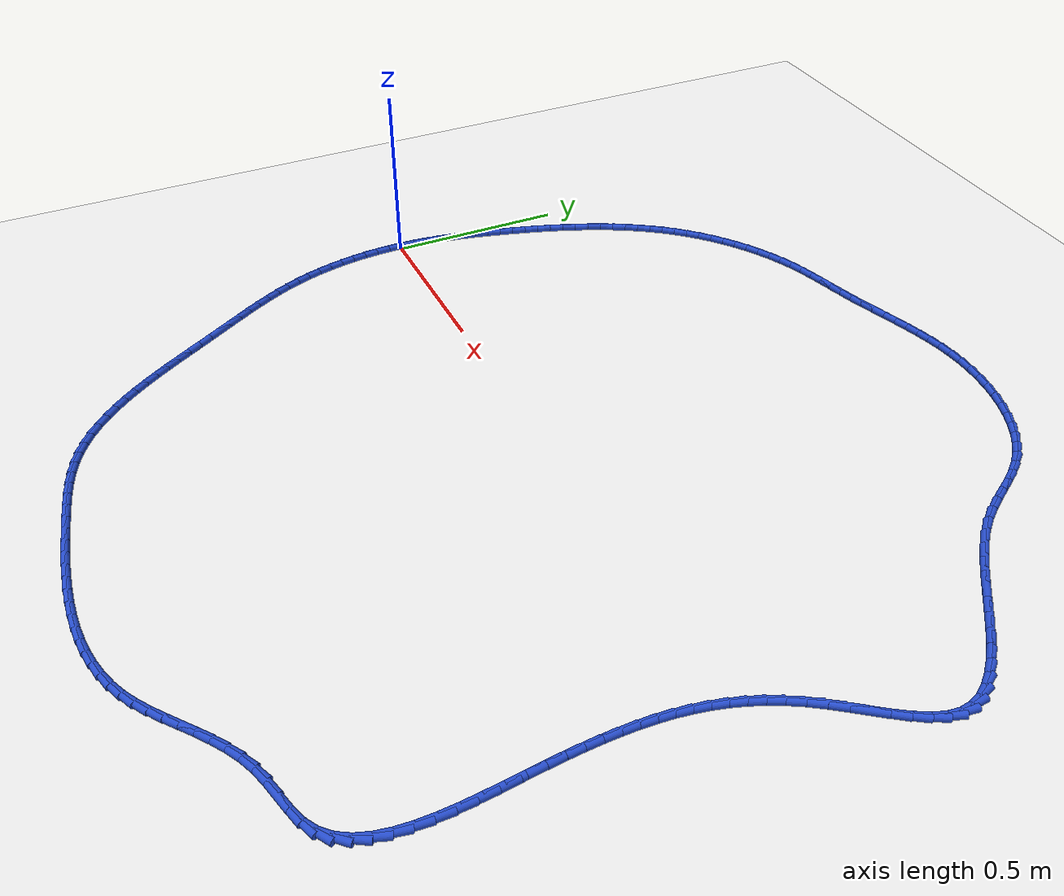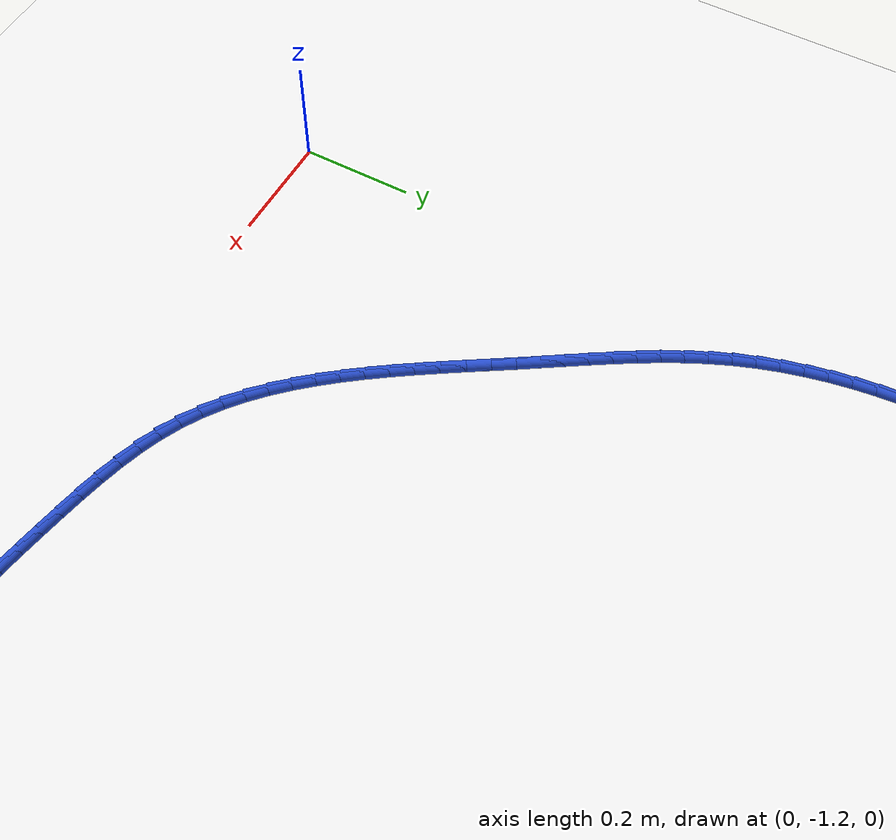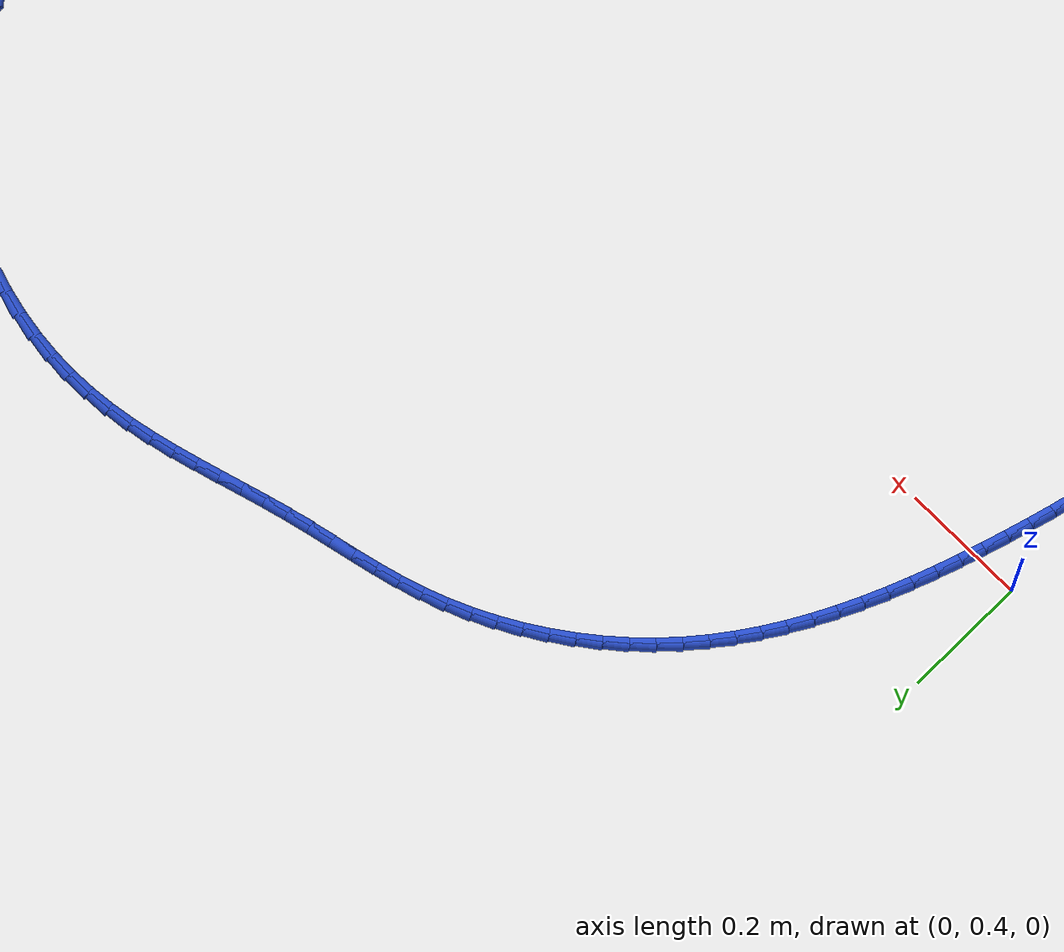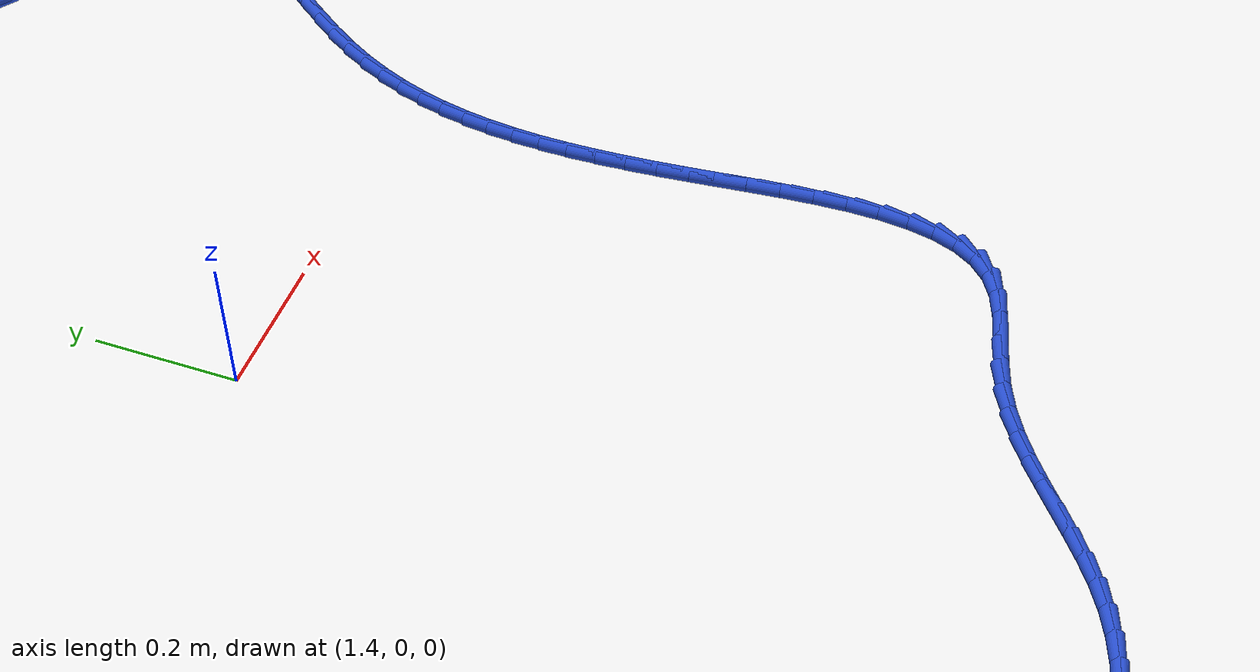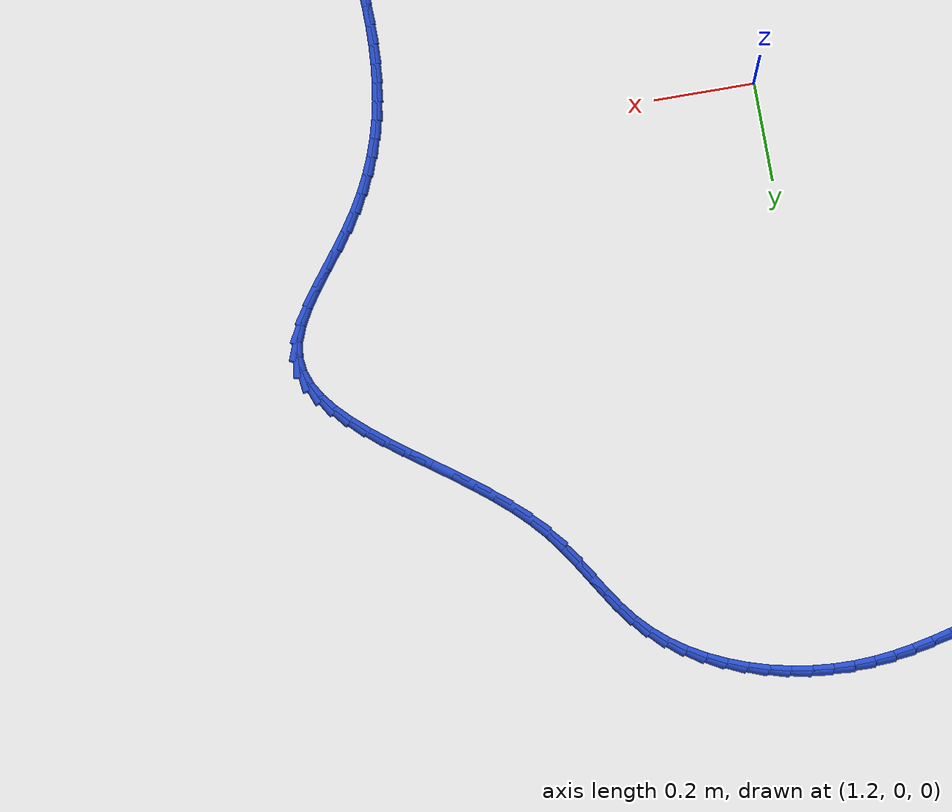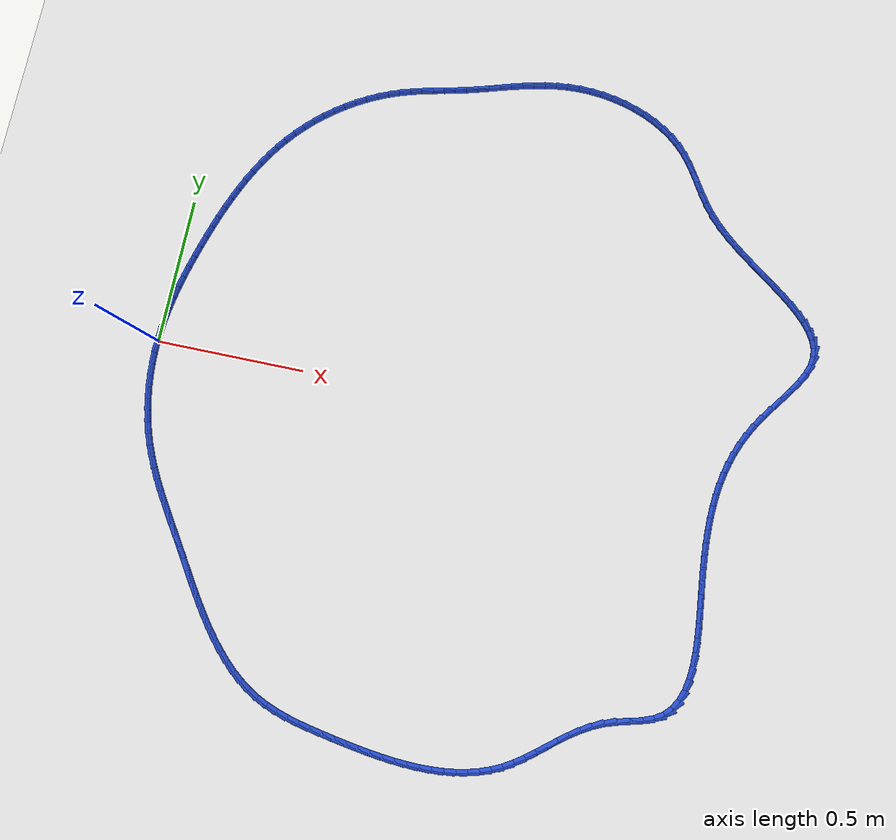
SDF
<sdf version="1.6">
 <world name="default">
  <light name="sun" type="directional">
   <pose>0 0 10 0 -0 0</pose>
   <diffuse>0.8 0.8 0.8 1</diffuse>
   <specular>0.2 0.2 0.2 1</specular>
   <attenuation>
    <range>1000</range>
    <constant>0.9</constant>
    <linear>0.01</linear>
    <quadratic>0.001</quadratic>
   </attenuation>
   <direction>-0.5 0.1 -0.9</direction>
  </light>
  <model name="ground_plane">
   <static>1</static>
   <link name="link">
    <collision name="collision">
     <geometry><plane><normal>0 0 1</normal><size>100 100</size></plane></geometry>
     <surface><friction><ode><mu>100</mu><mu2>50</mu2></ode></friction></surface>
    </collision>
    <visual name="visual">
     <cast_shadows>0</cast_shadows>
     <geometry><plane><normal>0 0 1</normal><size>100 100</size></plane></geometry>
     <material>
      <script><uri>file://media/materials/scripts/gazebo.material</uri><name>Gazebo/WhiteGlow</name></script>
     </material>
    </visual>
   </link>
  </model>
  <gravity>0 0 -9.8</gravity>
  <magnetic_field>6e-06 2.3e-05 -4.2e-05</magnetic_field>
  <atmosphere type="adiabatic"/>
  <physics name="default_physics" default="0" type="ode">
   <max_step_size>0.001</max_step_size>
   <real_time_factor>1</real_time_factor>
   <real_time_update_rate>1000</real_time_update_rate>
  </physics>
  <scene><ambient>0.4 0.4 0.4 1</ambient><background>0.7 0.7 0.7 1</background><shadows>1</shadows></scene>
  <spherical_coordinates>
   <surface_model>EARTH_WGS84</surface_model>
   <latitude_deg>0</latitude_deg>
   <longitude_deg>0</longitude_deg>
   <elevation>0</elevation>
   <heading_deg>0</heading_deg>
  </spherical_coordinates>
  <model name="line">
   <link name="link_0">
    <pose>0.0 -2.0816681711721685e-17 0.01 0 1.57 1.526415938484821</pose>
    <collision name="collision">
     <geometry><cylinder><radius>0.01</radius><length>0.08</length></cylinder></geometry>
    </collision>
    <visual name="visual">
     <material>
      <script><name>Gazebo/Blue</name><uri>file://media/materials/scripts/gazebo.material</uri></script>
     </material>
     <geometry><cylinder><radius>0.01</radius><length>0.08</length></cylinder></geometry>
    </visual>
   </link>
   <link name="link_1">
    <pose>0.001745237916421908 0.03929870860774991 0.01 0 1.57 1.4853059597841747</pose>
    <collision name="collision">
     <geometry><cylinder><radius>0.01</radius><length>0.08</length></cylinder></geometry>
    </collision>
    <visual name="visual">
     <material>
      <script><name>Gazebo/Blue</name><uri>file://media/materials/scripts/gazebo.material</uri></script>
     </material>
     <geometry><cylinder><radius>0.01</radius><length>0.08</length></cylinder></geometry>
    </visual>
   </link>
   <link name="link_2">
    <pose>0.005094811004305353 0.07838391777009533 0.01 0 1.57 1.4475610001432913</pose>
    <collision name="collision">
     <geometry><cylinder><radius>0.01</radius><length>0.08</length></cylinder></geometry>
    </collision>
    <visual name="visual">
     <material>
      <script><name>Gazebo/Blue</name><uri>file://media/materials/scripts/gazebo.material</uri></script>
     </material>
     <geometry><cylinder><radius>0.01</radius><length>0.08</length></cylinder></geometry>
    </visual>
   </link>
   <link name="link_3">
    <pose>0.009912469521488719 0.11727897662239475 0.01 0 1.57 1.4133252606400961</pose>
    <collision name="collision">
     <geometry><cylinder><radius>0.01</radius><length>0.08</length></cylinder></geometry>
    </collision>
    <visual name="visual">
     <material>
      <script><name>Gazebo/Blue</name><uri>file://media/materials/scripts/gazebo.material</uri></script>
     </material>
     <geometry><cylinder><radius>0.01</radius><length>0.08</length></cylinder></geometry>
    </visual>
   </link>
   <link name="link_4">
    <pose>0.01606196372581039 0.15600723430000685 0.01 0 1.57 1.3826850319097512</pose>
    <collision name="collision">
     <geometry><cylinder><radius>0.01</radius><length>0.08</length></cylinder></geometry>
    </collision>
    <visual name="visual">
     <material>
      <script><name>Gazebo/Blue</name><uri>file://media/materials/scripts/gazebo.material</uri></script>
     </material>
     <geometry><cylinder><radius>0.01</radius><length>0.08</length></cylinder></geometry>
    </visual>
   </link>
   <link name="link_5">
    <pose>0.023407043875108724 0.19459203993829013 0.01 0 1.57 1.3556802302046884</pose>
    <collision name="collision">
     <geometry><cylinder><radius>0.01</radius><length>0.08</length></cylinder></geometry>
    </collision>
    <visual name="visual">
     <material>
      <script><name>Gazebo/Blue</name><uri>file://media/materials/scripts/gazebo.material</uri></script>
     </material>
     <geometry><cylinder><radius>0.01</radius><length>0.08</length></cylinder></geometry>
    </visual>
   </link>
   <link name="link_6">
    <pose>0.03181146022722212 0.23305674267260318 0.01 0 1.57 1.3323159891005447</pose>
    <collision name="collision">
     <geometry><cylinder><radius>0.01</radius><length>0.08</length></cylinder></geometry>
    </collision>
    <visual name="visual">
     <material>
      <script><name>Gazebo/Blue</name><uri>file://media/materials/scripts/gazebo.material</uri></script>
     </material>
     <geometry><cylinder><radius>0.01</radius><length>0.08</length></cylinder></geometry>
    </visual>
   </link>
   <link name="link_7">
    <pose>0.04113896303998898 0.27142469163830474 0.01 0 1.57 1.312573411127895</pose>
    <collision name="collision">
     <geometry><cylinder><radius>0.01</radius><length>0.08</length></cylinder></geometry>
    </collision>
    <visual name="visual">
     <material>
      <script><name>Gazebo/Blue</name><uri>file://media/materials/scripts/gazebo.material</uri></script>
     </material>
     <geometry><cylinder><radius>0.01</radius><length>0.08</length></cylinder></geometry>
    </visual>
   </link>
   <link name="link_8">
    <pose>0.05125330257124765 0.30971923597075324 0.01 0 1.57 1.2964150245780186</pose>
    <collision name="collision">
     <geometry><cylinder><radius>0.01</radius><length>0.08</length></cylinder></geometry>
    </collision>
    <visual name="visual">
     <material>
      <script><name>Gazebo/Blue</name><uri>file://media/materials/scripts/gazebo.material</uri></script>
     </material>
     <geometry><cylinder><radius>0.01</radius><length>0.08</length></cylinder></geometry>
    </visual>
   </link>
   <link name="link_9">
    <pose>0.06201837070188188 0.34796365214294855 0.01 0 1.57 1.2822043983445515</pose>
    <collision name="collision">
     <geometry><cylinder><radius>0.01</radius><length>0.08</length></cylinder></geometry>
    </collision>
    <visual name="visual">
     <material>
      <script><name>Gazebo/Blue</name><uri>file://media/materials/scripts/gazebo.material</uri></script>
     </material>
     <geometry><cylinder><radius>0.01</radius><length>0.08</length></cylinder></geometry>
    </visual>
   </link>
   <link name="link_10">
    <pose>0.07335563078557984 0.3861516785043607 0.01 0 1.57 1.265858474856631</pose>
    <collision name="collision">
     <geometry><cylinder><radius>0.01</radius><length>0.08</length></cylinder></geometry>
    </collision>
    <visual name="visual">
     <material>
      <script><name>Gazebo/Blue</name><uri>file://media/materials/scripts/gazebo.material</uri></script>
     </material>
     <geometry><cylinder><radius>0.01</radius><length>0.08</length></cylinder></geometry>
    </visual>
   </link>
   <link name="link_11">
    <pose>0.08533225023353455 0.424202297205951 0.01 0 1.57 1.24669182617268</pose>
    <collision name="collision">
     <geometry><cylinder><radius>0.01</radius><length>0.08</length></cylinder></geometry>
    </collision>
    <visual name="visual">
     <material>
      <script><name>Gazebo/Blue</name><uri>file://media/materials/scripts/gazebo.material</uri></script>
     </material>
     <geometry><cylinder><radius>0.01</radius><length>0.08</length></cylinder></geometry>
    </visual>
   </link>
   <link name="link_12">
    <pose>0.09803809642492745 0.46202284375450264 0.01 0 1.57 1.2246334604833622</pose>
    <collision name="collision">
     <geometry><cylinder><radius>0.01</radius><length>0.08</length></cylinder></geometry>
    </collision>
    <visual name="visual">
     <material>
      <script><name>Gazebo/Blue</name><uri>file://media/materials/scripts/gazebo.material</uri></script>
     </material>
     <geometry><cylinder><radius>0.01</radius><length>0.08</length></cylinder></geometry>
    </visual>
   </link>
   <link name="link_13">
    <pose>0.1115630367389401 0.4995206536567991 0.01 0 1.57 1.199601374923215</pose>
    <collision name="collision">
     <geometry><cylinder><radius>0.01</radius><length>0.08</length></cylinder></geometry>
    </collision>
    <visual name="visual">
     <material>
      <script><name>Gazebo/Blue</name><uri>file://media/materials/scripts/gazebo.material</uri></script>
     </material>
     <geometry><cylinder><radius>0.01</radius><length>0.08</length></cylinder></geometry>
    </visual>
   </link>
   <link name="link_14">
    <pose>0.1259969385547538 0.5366030624196231 0.01 0 1.57 1.1715075593788333</pose>
    <collision name="collision">
     <geometry><cylinder><radius>0.01</radius><length>0.08</length></cylinder></geometry>
    </collision>
    <visual name="visual">
     <material>
      <script><name>Gazebo/Blue</name><uri>file://media/materials/scripts/gazebo.material</uri></script>
     </material>
     <geometry><cylinder><radius>0.01</radius><length>0.08</length></cylinder></geometry>
    </visual>
   </link>
   <link name="link_15">
    <pose>0.14142966925155018 0.5731774055497585 0.01 0 1.57 1.140264263077125</pose>
    <collision name="collision">
     <geometry><cylinder><radius>0.01</radius><length>0.08</length></cylinder></geometry>
    </collision>
    <visual name="visual">
     <material>
      <script><name>Gazebo/Blue</name><uri>file://media/materials/scripts/gazebo.material</uri></script>
     </material>
     <geometry><cylinder><radius>0.01</radius><length>0.08</length></cylinder></geometry>
    </visual>
   </link>
   <link name="link_16">
    <pose>0.15795109620851056 0.6091510185539878 0.01 0 1.57 1.105791793319847</pose>
    <collision name="collision">
     <geometry><cylinder><radius>0.01</radius><length>0.08</length></cylinder></geometry>
    </collision>
    <visual name="visual">
     <material>
      <script><name>Gazebo/Blue</name><uri>file://media/materials/scripts/gazebo.material</uri></script>
     </material>
     <geometry><cylinder><radius>0.01</radius><length>0.08</length></cylinder></geometry>
    </visual>
   </link>
   <link name="link_17">
    <pose>0.17565108680481645 0.6444312369390945 0.01 0 1.57 1.0680280374248856</pose>
    <collision name="collision">
     <geometry><cylinder><radius>0.01</radius><length>0.08</length></cylinder></geometry>
    </collision>
    <visual name="visual">
     <material>
      <script><name>Gazebo/Blue</name><uri>file://media/materials/scripts/gazebo.material</uri></script>
     </material>
     <geometry><cylinder><radius>0.01</radius><length>0.08</length></cylinder></geometry>
    </visual>
   </link>
   <link name="link_18">
    <pose>0.1946195084196494 0.6789253962118622 0.01 0 1.57 1.0269397396952495</pose>
    <collision name="collision">
     <geometry><cylinder><radius>0.01</radius><length>0.08</length></cylinder></geometry>
    </collision>
    <visual name="visual">
     <material>
      <script><name>Gazebo/Blue</name><uri>file://media/materials/scripts/gazebo.material</uri></script>
     </material>
     <geometry><cylinder><radius>0.01</radius><length>0.08</length></cylinder></geometry>
    </visual>
   </link>
   <link name="link_19">
    <pose>0.21494622843219074 0.7125408318790735 0.01 0 1.57 0.982535299894861</pose>
    <collision name="collision">
     <geometry><cylinder><radius>0.01</radius><length>0.08</length></cylinder></geometry>
    </collision>
    <visual name="visual">
     <material>
      <script><name>Gazebo/Blue</name><uri>file://media/materials/scripts/gazebo.material</uri></script>
     </material>
     <geometry><cylinder><radius>0.01</radius><length>0.08</length></cylinder></geometry>
    </visual>
   </link>
   <link name="link_20">
    <pose>0.23672111422162204 0.745184879447512 0.01 0 1.57 0.9348784759147478</pose>
    <collision name="collision">
     <geometry><cylinder><radius>0.01</radius><length>0.08</length></cylinder></geometry>
    </collision>
    <visual name="visual">
     <material>
      <script><name>Gazebo/Blue</name><uri>file://media/materials/scripts/gazebo.material</uri></script>
     </material>
     <geometry><cylinder><radius>0.01</radius><length>0.08</length></cylinder></geometry>
    </visual>
   </link>
   <link name="link_21">
    <pose>0.2600340331671247 0.7767648744239607 0.01 0 1.57 0.8841018892397132</pose>
    <collision name="collision">
     <geometry><cylinder><radius>0.01</radius><length>0.08</length></cylinder></geometry>
    </collision>
    <visual name="visual">
     <material>
      <script><name>Gazebo/Blue</name><uri>file://media/materials/scripts/gazebo.material</uri></script>
     </material>
     <geometry><cylinder><radius>0.01</radius><length>0.08</length></cylinder></geometry>
    </visual>
   </link>
   <link name="link_22">
    <pose>0.2849748526478802 0.807188152315203 0.01 0 1.57 0.831065877662476</pose>
    <collision name="collision">
     <geometry><cylinder><radius>0.01</radius><length>0.08</length></cylinder></geometry>
    </collision>
    <visual name="visual">
     <material>
      <script><name>Gazebo/Blue</name><uri>file://media/materials/scripts/gazebo.material</uri></script>
     </material>
     <geometry><cylinder><radius>0.01</radius><length>0.08</length></cylinder></geometry>
    </visual>
   </link>
   <link name="link_23">
    <pose>0.3115999284305398 0.8363632682947683 0.01 0 1.57 0.7784731479066586</pose>
    <collision name="collision">
     <geometry><cylinder><radius>0.01</radius><length>0.08</length></cylinder></geometry>
    </collision>
    <visual name="visual">
     <material>
      <script><name>Gazebo/Blue</name><uri>file://media/materials/scripts/gazebo.material</uri></script>
     </material>
     <geometry><cylinder><radius>0.01</radius><length>0.08</length></cylinder></geometry>
    </visual>
   </link>
   <link name="link_24">
    <pose>0.339828707298666 0.8642037603860506 0.01 0 1.57 0.726747478106805</pose>
    <collision name="collision">
     <geometry><cylinder><radius>0.01</radius><length>0.08</length></cylinder></geometry>
    </collision>
    <visual name="visual">
     <material>
      <script><name>Gazebo/Blue</name><uri>file://media/materials/scripts/gazebo.material</uri></script>
     </material>
     <geometry><cylinder><radius>0.01</radius><length>0.08</length></cylinder></geometry>
    </visual>
   </link>
   <link name="link_25">
    <pose>0.3695456779407081 0.8906244389244257 0.01 0 1.57 0.6756024190688973</pose>
    <collision name="collision">
     <geometry><cylinder><radius>0.01</radius><length>0.08</length></cylinder></geometry>
    </collision>
    <visual name="visual">
     <material>
      <script><name>Gazebo/Blue</name><uri>file://media/materials/scripts/gazebo.material</uri></script>
     </material>
     <geometry><cylinder><radius>0.01</radius><length>0.08</length></cylinder></geometry>
    </visual>
   </link>
   <link name="link_26">
    <pose>0.40063532903315574 0.9155401142457036 0.01 0 1.57 0.6247509940801138</pose>
    <collision name="collision">
     <geometry><cylinder><radius>0.01</radius><length>0.08</length></cylinder></geometry>
    </collision>
    <visual name="visual">
     <material>
      <script><name>Gazebo/Blue</name><uri>file://media/materials/scripts/gazebo.material</uri></script>
     </material>
     <geometry><cylinder><radius>0.01</radius><length>0.08</length></cylinder></geometry>
    </visual>
   </link>
   <link name="link_27">
    <pose>0.43298214925249834 0.9388655966856944 0.01 0 1.57 0.5739065913421142</pose>
    <collision name="collision">
     <geometry><cylinder><radius>0.01</radius><length>0.08</length></cylinder></geometry>
    </collision>
    <visual name="visual">
     <material>
      <script><name>Gazebo/Blue</name><uri>file://media/materials/scripts/gazebo.material</uri></script>
     </material>
     <geometry><cylinder><radius>0.01</radius><length>0.08</length></cylinder></geometry>
    </visual>
   </link>
   <link name="link_28">
    <pose>0.46647062727522653 0.9605156965802091 0.01 0 1.57 0.5227835188963549</pose>
    <collision name="collision">
     <geometry><cylinder><radius>0.01</radius><length>0.08</length></cylinder></geometry>
    </collision>
    <visual name="visual">
     <material>
      <script><name>Gazebo/Blue</name><uri>file://media/materials/scripts/gazebo.material</uri></script>
     </material>
     <geometry><cylinder><radius>0.01</radius><length>0.08</length></cylinder></geometry>
    </visual>
   </link>
   <link name="link_29">
    <pose>0.5009852517778299 0.9804052242650584 0.01 0 1.57 0.47109757847331624</pose>
    <collision name="collision">
     <geometry><cylinder><radius>0.01</radius><length>0.08</length></cylinder></geometry>
    </collision>
    <visual name="visual">
     <material>
      <script><name>Gazebo/Blue</name><uri>file://media/materials/scripts/gazebo.material</uri></script>
     </material>
     <geometry><cylinder><radius>0.01</radius><length>0.08</length></cylinder></geometry>
    </visual>
   </link>
   <link name="link_30">
    <pose>0.536410511436798 0.998448990076052 0.01 0 1.57 0.41856701039395044</pose>
    <collision name="collision">
     <geometry><cylinder><radius>0.01</radius><length>0.08</length></cylinder></geometry>
    </collision>
    <visual name="visual">
     <material>
      <script><name>Gazebo/Blue</name><uri>file://media/materials/scripts/gazebo.material</uri></script>
     </material>
     <geometry><cylinder><radius>0.01</radius><length>0.08</length></cylinder></geometry>
    </visual>
   </link>
   <link name="link_31">
    <pose>0.5726308949286207 1.0145618043490008 0.01 0 1.57 0.3649141724647435</pose>
    <collision name="collision">
     <geometry><cylinder><radius>0.01</radius><length>0.08</length></cylinder></geometry>
    </collision>
    <visual name="visual">
     <material>
      <script><name>Gazebo/Blue</name><uri>file://media/materials/scripts/gazebo.material</uri></script>
     </material>
     <geometry><cylinder><radius>0.01</radius><length>0.08</length></cylinder></geometry>
    </visual>
   </link>
   <link name="link_32">
    <pose>0.6095308909297883 1.028658477419715 0.01 0 1.57 0.31117854952049984</pose>
    <collision name="collision">
     <geometry><cylinder><radius>0.01</radius><length>0.08</length></cylinder></geometry>
    </collision>
    <visual name="visual">
     <material>
      <script><name>Gazebo/Blue</name><uri>file://media/materials/scripts/gazebo.material</uri></script>
     </material>
     <geometry><cylinder><radius>0.01</radius><length>0.08</length></cylinder></geometry>
    </visual>
   </link>
   <link name="link_33">
    <pose>0.6469924354882246 1.0407071394653227 0.01 0 1.57 0.26738921731400006</pose>
    <collision name="collision">
     <geometry><cylinder><radius>0.01</radius><length>0.08</length></cylinder></geometry>
    </collision>
    <visual name="visual">
     <material>
      <script><name>Gazebo/Blue</name><uri>file://media/materials/scripts/gazebo.material</uri></script>
     </material>
     <geometry><cylinder><radius>0.01</radius><length>0.08</length></cylinder></geometry>
    </visual>
   </link>
   <link name="link_34">
    <pose>0.6848778409965444 1.0510858236943426 0.01 0 1.57 0.23846284457718867</pose>
    <collision name="collision">
     <geometry><cylinder><radius>0.01</radius><length>0.08</length></cylinder></geometry>
    </collision>
    <visual name="visual">
     <material>
      <script><name>Gazebo/Blue</name><uri>file://media/materials/scripts/gazebo.material</uri></script>
     </material>
     <geometry><cylinder><radius>0.01</radius><length>0.08</length></cylinder></geometry>
    </visual>
   </link>
   <link name="link_35">
    <pose>0.7230403187919666 1.0603626680708635 0.01 0 1.57 0.22450182062747284</pose>
    <collision name="collision">
     <geometry><cylinder><radius>0.01</radius><length>0.08</length></cylinder></geometry>
    </collision>
    <visual name="visual">
     <material>
      <script><name>Gazebo/Blue</name><uri>file://media/materials/scripts/gazebo.material</uri></script>
     </material>
     <geometry><cylinder><radius>0.01</radius><length>0.08</length></cylinder></geometry>
    </visual>
   </link>
   <link name="link_36">
    <pose>0.7613330303091386 1.0691068529343584 0.01 0 1.57 0.2255025990860086</pose>
    <collision name="collision">
     <geometry><cylinder><radius>0.01</radius><length>0.08</length></cylinder></geometry>
    </collision>
    <visual name="visual">
     <material>
      <script><name>Gazebo/Blue</name><uri>file://media/materials/scripts/gazebo.material</uri></script>
     </material>
     <geometry><cylinder><radius>0.01</radius><length>0.08</length></cylinder></geometry>
    </visual>
   </link>
   <link name="link_37">
    <pose>0.7996091369827074 1.0778875586243009 0.01 0 1.57 0.241440266440755</pose>
    <collision name="collision">
     <geometry><cylinder><radius>0.01</radius><length>0.08</length></cylinder></geometry>
    </collision>
    <visual name="visual">
     <material>
      <script><name>Gazebo/Blue</name><uri>file://media/materials/scripts/gazebo.material</uri></script>
     </material>
     <geometry><cylinder><radius>0.01</radius><length>0.08</length></cylinder></geometry>
    </visual>
   </link>
   <link name="link_38">
    <pose>0.8377221427799659 1.0872726485000026 0.01 0 1.57 0.26519665062997594</pose>
    <collision name="collision">
     <geometry><cylinder><radius>0.01</radius><length>0.08</length></cylinder></geometry>
    </collision>
    <visual name="visual">
     <material>
      <script><name>Gazebo/Blue</name><uri>file://media/materials/scripts/gazebo.material</uri></script>
     </material>
     <geometry><cylinder><radius>0.01</radius><length>0.08</length></cylinder></geometry>
    </visual>
   </link>
   <link name="link_39">
    <pose>0.8755960423897138 1.0975589610039074 0.01 0 1.57 0.2809432589860825</pose>
    <collision name="collision">
     <geometry><cylinder><radius>0.01</radius><length>0.08</length></cylinder></geometry>
    </collision>
    <visual name="visual">
     <material>
      <script><name>Gazebo/Blue</name><uri>file://media/materials/scripts/gazebo.material</uri></script>
     </material>
     <geometry><cylinder><radius>0.01</radius><length>0.08</length></cylinder></geometry>
    </visual>
   </link>
   <link name="link_40">
    <pose>0.9133110730595467 1.108442608332455 0.01 0 1.57 0.28655785855542054</pose>
    <collision name="collision">
     <geometry><cylinder><radius>0.01</radius><length>0.08</length></cylinder></geometry>
    </collision>
    <visual name="visual">
     <material>
      <script><name>Gazebo/Blue</name><uri>file://media/materials/scripts/gazebo.material</uri></script>
     </material>
     <geometry><cylinder><radius>0.01</radius><length>0.08</length></cylinder></geometry>
    </visual>
   </link>
   <link name="link_41">
    <pose>0.9509684537262798 1.1195390316312674 0.01 0 1.57 0.2820461383885123</pose>
    <collision name="collision">
     <geometry><cylinder><radius>0.01</radius><length>0.08</length></cylinder></geometry>
    </collision>
    <visual name="visual">
     <material>
      <script><name>Gazebo/Blue</name><uri>file://media/materials/scripts/gazebo.material</uri></script>
     </material>
     <geometry><cylinder><radius>0.01</radius><length>0.08</length></cylinder></geometry>
    </visual>
   </link>
   <link name="link_42">
    <pose>0.9886694033267295 1.1304636720459682 0.01 0 1.57 0.2674010513809448</pose>
    <collision name="collision">
     <geometry><cylinder><radius>0.01</radius><length>0.08</length></cylinder></geometry>
    </collision>
    <visual name="visual">
     <material>
      <script><name>Gazebo/Blue</name><uri>file://media/materials/scripts/gazebo.material</uri></script>
     </material>
     <geometry><cylinder><radius>0.01</radius><length>0.08</length></cylinder></geometry>
    </visual>
   </link>
   <link name="link_43">
    <pose>1.0265151407977111 1.1408319707221803 0.01 0 1.57 0.24261670688565298</pose>
    <collision name="collision">
     <geometry><cylinder><radius>0.01</radius><length>0.08</length></cylinder></geometry>
    </collision>
    <visual name="visual">
     <material>
      <script><name>Gazebo/Blue</name><uri>file://media/materials/scripts/gazebo.material</uri></script>
     </material>
     <geometry><cylinder><radius>0.01</radius><length>0.08</length></cylinder></geometry>
    </visual>
   </link>
   <link name="link_44">
    <pose>1.0646068850760408 1.150259368805527 0.01 0 1.57 0.20773346592808328</pose>
    <collision name="collision">
     <geometry><cylinder><radius>0.01</radius><length>0.08</length></cylinder></geometry>
    </collision>
    <visual name="visual">
     <material>
      <script><name>Gazebo/Blue</name><uri>file://media/materials/scripts/gazebo.material</uri></script>
     </material>
     <geometry><cylinder><radius>0.01</radius><length>0.08</length></cylinder></geometry>
    </visual>
   </link>
   <link name="link_45">
    <pose>1.1030458550985338 1.1583613074416304 0.01 0 1.57 0.16291315333399758</pose>
    <collision name="collision">
     <geometry><cylinder><radius>0.01</radius><length>0.08</length></cylinder></geometry>
    </collision>
    <visual name="visual">
     <material>
      <script><name>Gazebo/Blue</name><uri>file://media/materials/scripts/gazebo.material</uri></script>
     </material>
     <geometry><cylinder><radius>0.01</radius><length>0.08</length></cylinder></geometry>
    </visual>
   </link>
   <link name="link_46">
    <pose>1.1419332698020068 1.1647532277761146 0.01 0 1.57 0.10853883920037315</pose>
    <collision name="collision">
     <geometry><cylinder><radius>0.01</radius><length>0.08</length></cylinder></geometry>
    </collision>
    <visual name="visual">
     <material>
      <script><name>Gazebo/Blue</name><uri>file://media/materials/scripts/gazebo.material</uri></script>
     </material>
     <geometry><cylinder><radius>0.01</radius><length>0.08</length></cylinder></geometry>
    </visual>
   </link>
   <link name="link_47">
    <pose>1.1813703481232751 1.1690505709546015 0.01 0 1.57 0.04533581515027767</pose>
    <collision name="collision">
     <geometry><cylinder><radius>0.01</radius><length>0.08</length></cylinder></geometry>
    </collision>
    <visual name="visual">
     <material>
      <script><name>Gazebo/Blue</name><uri>file://media/materials/scripts/gazebo.material</uri></script>
     </material>
     <geometry><cylinder><radius>0.01</radius><length>0.08</length></cylinder></geometry>
    </visual>
   </link>
   <link name="link_48">
    <pose>1.2214577972305813 1.170869214282386 0.01 0 1.57 -0.022891678467195725</pose>
    <collision name="collision">
     <geometry><cylinder><radius>0.01</radius><length>0.08</length></cylinder></geometry>
    </collision>
    <visual name="visual">
     <material>
      <script><name>Gazebo/Blue</name><uri>file://media/materials/scripts/gazebo.material</uri></script>
     </material>
     <geometry><cylinder><radius>0.01</radius><length>0.08</length></cylinder></geometry>
    </visual>
   </link>
   <link name="link_49">
    <pose>1.262164713242165 1.1699372018434722 0.01 0 1.57 -0.08987571435881217</pose>
    <collision name="collision">
     <geometry><cylinder><radius>0.01</radius><length>0.08</length></cylinder></geometry>
    </collision>
    <visual name="visual">
     <material>
      <script><name>Gazebo/Blue</name><uri>file://media/materials/scripts/gazebo.material</uri></script>
     </material>
     <geometry><cylinder><radius>0.01</radius><length>0.08</length></cylinder></geometry>
    </visual>
   </link>
   <link name="link_50">
    <pose>1.3031542938465537 1.1662432825902787 0.01 0 1.57 -0.15596903619288768</pose>
    <collision name="collision">
     <geometry><cylinder><radius>0.01</radius><length>0.08</length></cylinder></geometry>
    </collision>
    <visual name="visual">
     <material>
      <script><name>Gazebo/Blue</name><uri>file://media/materials/scripts/gazebo.material</uri></script>
     </material>
     <geometry><cylinder><radius>0.01</radius><length>0.08</length></cylinder></geometry>
    </visual>
   </link>
   <link name="link_51">
    <pose>1.3440463779305294 1.1598131584295597 0.01 0 1.57 -0.22243005335612195</pose>
    <collision name="collision">
     <geometry><cylinder><radius>0.01</radius><length>0.08</length></cylinder></geometry>
    </collision>
    <visual name="visual">
     <material>
      <script><name>Gazebo/Blue</name><uri>file://media/materials/scripts/gazebo.material</uri></script>
     </material>
     <geometry><cylinder><radius>0.01</radius><length>0.08</length></cylinder></geometry>
    </visual>
   </link>
   <link name="link_52">
    <pose>1.3844608043808728 1.1506725312680683 0.01 0 1.57 -0.2904927583099985</pose>
    <collision name="collision">
     <geometry><cylinder><radius>0.01</radius><length>0.08</length></cylinder></geometry>
    </collision>
    <visual name="visual">
     <material>
      <script><name>Gazebo/Blue</name><uri>file://media/materials/scripts/gazebo.material</uri></script>
     </material>
     <geometry><cylinder><radius>0.01</radius><length>0.08</length></cylinder></geometry>
    </visual>
   </link>
   <link name="link_53">
    <pose>1.4240174120843647 1.1388471030125598 0.01 0 1.57 -0.36140017610113045</pose>
    <collision name="collision">
     <geometry><cylinder><radius>0.01</radius><length>0.08</length></cylinder></geometry>
    </collision>
    <visual name="visual">
     <material>
      <script><name>Gazebo/Blue</name><uri>file://media/materials/scripts/gazebo.material</uri></script>
     </material>
     <geometry><cylinder><radius>0.01</radius><length>0.08</length></cylinder></geometry>
    </visual>
   </link>
   <link name="link_54">
    <pose>1.4623360399277854 1.1243625755697872 0.01 0 1.57 -0.4364264576479031</pose>
    <collision name="collision">
     <geometry><cylinder><radius>0.01</radius><length>0.08</length></cylinder></geometry>
    </collision>
    <visual name="visual">
     <material>
      <script><name>Gazebo/Blue</name><uri>file://media/materials/scripts/gazebo.material</uri></script>
     </material>
     <geometry><cylinder><radius>0.01</radius><length>0.08</length></cylinder></geometry>
    </visual>
   </link>
   <link name="link_55">
    <pose>1.499036526797916 1.1072446508465044 0.01 0 1.57 -0.5168796228794665</pose>
    <collision name="collision">
     <geometry><cylinder><radius>0.01</radius><length>0.08</length></cylinder></geometry>
    </collision>
    <visual name="visual">
     <material>
      <script><name>Gazebo/Blue</name><uri>file://media/materials/scripts/gazebo.material</uri></script>
     </material>
     <geometry><cylinder><radius>0.01</radius><length>0.08</length></cylinder></geometry>
    </visual>
   </link>
   <link name="link_56">
    <pose>1.533738711581538 1.087519030749466 0.01 0 1.57 -0.604071956234662</pose>
    <collision name="collision">
     <geometry><cylinder><radius>0.01</radius><length>0.08</length></cylinder></geometry>
    </collision>
    <visual name="visual">
     <material>
      <script><name>Gazebo/Blue</name><uri>file://media/materials/scripts/gazebo.material</uri></script>
     </material>
     <geometry><cylinder><radius>0.01</radius><length>0.08</length></cylinder></geometry>
    </visual>
   </link>
   <link name="link_57">
    <pose>1.5660624331654307 1.0652114171854252 0.01 0 1.57 -0.6992390707674084</pose>
    <collision name="collision">
     <geometry><cylinder><radius>0.01</radius><length>0.08</length></cylinder></geometry>
    </collision>
    <visual name="visual">
     <material>
      <script><name>Gazebo/Blue</name><uri>file://media/materials/scripts/gazebo.material</uri></script>
     </material>
     <geometry><cylinder><radius>0.01</radius><length>0.08</length></cylinder></geometry>
    </visual>
   </link>
   <link name="link_58">
    <pose>1.5956275304363765 1.040347512061137 0.01 0 1.57 -0.8032128525421833</pose>
    <collision name="collision">
     <geometry><cylinder><radius>0.01</radius><length>0.08</length></cylinder></geometry>
    </collision>
    <visual name="visual">
     <material>
      <script><name>Gazebo/Blue</name><uri>file://media/materials/scripts/gazebo.material</uri></script>
     </material>
     <geometry><cylinder><radius>0.01</radius><length>0.08</length></cylinder></geometry>
    </visual>
   </link>
   <link name="link_59">
    <pose>1.622060587713493 1.0129554760281962 0.01 0 1.57 -0.9026111284371222</pose>
    <collision name="collision">
     <geometry><cylinder><radius>0.01</radius><length>0.08</length></cylinder></geometry>
    </collision>
    <visual name="visual">
     <material>
      <script><name>Gazebo/Blue</name><uri>file://media/materials/scripts/gazebo.material</uri></script>
     </material>
     <geometry><cylinder><radius>0.01</radius><length>0.08</length></cylinder></geometry>
    </visual>
   </link>
   <link name="link_60">
    <pose>1.6455056166699857 0.9832520746747376 0.01 0 1.57 -0.9721071338292425</pose>
    <collision name="collision">
     <geometry><cylinder><radius>0.01</radius><length>0.08</length></cylinder></geometry>
    </collision>
    <visual name="visual">
     <material>
      <script><name>Gazebo/Blue</name><uri>file://media/materials/scripts/gazebo.material</uri></script>
     </material>
     <geometry><cylinder><radius>0.01</radius><length>0.08</length></cylinder></geometry>
    </visual>
   </link>
   <link name="link_61">
    <pose>1.6669811878000569 0.951772854785194 0.01 0 1.57 -1.0082771171789278</pose>
    <collision name="collision">
     <geometry><cylinder><radius>0.01</radius><length>0.08</length></cylinder></geometry>
    </collision>
    <visual name="visual">
     <material>
      <script><name>Gazebo/Blue</name><uri>file://media/materials/scripts/gazebo.material</uri></script>
     </material>
     <geometry><cylinder><radius>0.01</radius><length>0.08</length></cylinder></geometry>
    </visual>
   </link>
   <link name="link_62">
    <pose>1.6875902707785475 0.919084127080195 0.01 0 1.57 -1.0119141946341264</pose>
    <collision name="collision">
     <geometry><cylinder><radius>0.01</radius><length>0.08</length></cylinder></geometry>
    </collision>
    <visual name="visual">
     <material>
      <script><name>Gazebo/Blue</name><uri>file://media/materials/scripts/gazebo.material</uri></script>
     </material>
     <geometry><cylinder><radius>0.01</radius><length>0.08</length></cylinder></geometry>
    </visual>
   </link>
   <link name="link_63">
    <pose>1.7084358352802989 0.8857522022803708 0.01 0 1.57 -0.9846096387332908</pose>
    <collision name="collision">
     <geometry><cylinder><radius>0.01</radius><length>0.08</length></cylinder></geometry>
    </collision>
    <visual name="visual">
     <material>
      <script><name>Gazebo/Blue</name><uri>file://media/materials/scripts/gazebo.material</uri></script>
     </material>
     <geometry><cylinder><radius>0.01</radius><length>0.08</length></cylinder></geometry>
    </visual>
   </link>
   <link name="link_64">
    <pose>1.73062085098015 0.8523433911063516 0.01 0 1.57 -0.9285036935971838</pose>
    <collision name="collision">
     <geometry><cylinder><radius>0.01</radius><length>0.08</length></cylinder></geometry>
    </collision>
    <visual name="visual">
     <material>
      <script><name>Gazebo/Blue</name><uri>file://media/materials/scripts/gazebo.material</uri></script>
     </material>
     <geometry><cylinder><radius>0.01</radius><length>0.08</length></cylinder></geometry>
    </visual>
   </link>
   <link name="link_65">
    <pose>1.7552482875529432 0.8194240042787682 0.01 0 1.57 -0.848129932686067</pose>
    <collision name="collision">
     <geometry><cylinder><radius>0.01</radius><length>0.08</length></cylinder></geometry>
    </collision>
    <visual name="visual">
     <material>
      <script><name>Gazebo/Blue</name><uri>file://media/materials/scripts/gazebo.material</uri></script>
     </material>
     <geometry><cylinder><radius>0.01</radius><length>0.08</length></cylinder></geometry>
    </visual>
   </link>
   <link name="link_66">
    <pose>1.7833644824527948 0.7875388749199437 0.01 0 1.57 -0.769747486345621</pose>
    <collision name="collision">
     <geometry><cylinder><radius>0.01</radius><length>0.08</length></cylinder></geometry>
    </collision>
    <visual name="visual">
     <material>
      <script><name>Gazebo/Blue</name><uri>file://media/materials/scripts/gazebo.material</uri></script>
     </material>
     <geometry><cylinder><radius>0.01</radius><length>0.08</length></cylinder></geometry>
    </visual>
   </link>
   <link name="link_67">
    <pose>1.8150228444236751 0.7568562709440844 0.01 0 1.57 -0.7109773756098754</pose>
    <collision name="collision">
     <geometry><cylinder><radius>0.01</radius><length>0.08</length></cylinder></geometry>
    </collision>
    <visual name="visual">
     <material>
      <script><name>Gazebo/Blue</name><uri>file://media/materials/scripts/gazebo.material</uri></script>
     </material>
     <geometry><cylinder><radius>0.01</radius><length>0.08</length></cylinder></geometry>
    </visual>
   </link>
   <link name="link_68">
    <pose>1.8494303960761866 0.7272234708859927 0.01 0 1.57 -0.6692913121242292</pose>
    <collision name="collision">
     <geometry><cylinder><radius>0.01</radius><length>0.08</length></cylinder></geometry>
    </collision>
    <visual name="visual">
     <material>
      <script><name>Gazebo/Blue</name><uri>file://media/materials/scripts/gazebo.material</uri></script>
     </material>
     <geometry><cylinder><radius>0.01</radius><length>0.08</length></cylinder></geometry>
    </visual>
   </link>
   <link name="link_69">
    <pose>1.8857670707859722 0.698477479770101 0.01 0 1.57 -0.6424385245916124</pose>
    <collision name="collision">
     <geometry><cylinder><radius>0.01</radius><length>0.08</length></cylinder></geometry>
    </collision>
    <visual name="visual">
     <material>
      <script><name>Gazebo/Blue</name><uri>file://media/materials/scripts/gazebo.material</uri></script>
     </material>
     <geometry><cylinder><radius>0.01</radius><length>0.08</length></cylinder></geometry>
    </visual>
   </link>
   <link name="link_70">
    <pose>1.9232128019286698 0.6704553026208415 0.01 0 1.57 -0.6291069048368725</pose>
    <collision name="collision">
     <geometry><cylinder><radius>0.01</radius><length>0.08</length></cylinder></geometry>
    </collision>
    <visual name="visual">
     <material>
      <script><name>Gazebo/Blue</name><uri>file://media/materials/scripts/gazebo.material</uri></script>
     </material>
     <geometry><cylinder><radius>0.01</radius><length>0.08</length></cylinder></geometry>
    </visual>
   </link>
   <link name="link_71">
    <pose>1.960947522879923 0.6429939444626462 0.01 0 1.57 -0.6289077089782888</pose>
    <collision name="collision">
     <geometry><cylinder><radius>0.01</radius><length>0.08</length></cylinder></geometry>
    </collision>
    <visual name="visual">
     <material>
      <script><name>Gazebo/Blue</name><uri>file://media/materials/scripts/gazebo.material</uri></script>
     </material>
     <geometry><cylinder><radius>0.01</radius><length>0.08</length></cylinder></geometry>
    </visual>
   </link>
   <link name="link_72">
    <pose>1.99815116701537 0.6159304103199474 0.01 0 1.57 -0.6424172062147037</pose>
    <collision name="collision">
     <geometry><cylinder><radius>0.01</radius><length>0.08</length></cylinder></geometry>
    </collision>
    <visual name="visual">
     <material>
      <script><name>Gazebo/Blue</name><uri>file://media/materials/scripts/gazebo.material</uri></script>
     </material>
     <geometry><cylinder><radius>0.01</radius><length>0.08</length></cylinder></geometry>
    </visual>
   </link>
   <link name="link_73">
    <pose>2.034003667710653 0.5891017052171773 0.01 0 1.57 -0.6713252278008757</pose>
    <collision name="collision">
     <geometry><cylinder><radius>0.01</radius><length>0.08</length></cylinder></geometry>
    </collision>
    <visual name="visual">
     <material>
      <script><name>Gazebo/Blue</name><uri>file://media/materials/scripts/gazebo.material</uri></script>
     </material>
     <geometry><cylinder><radius>0.01</radius><length>0.08</length></cylinder></geometry>
    </visual>
   </link>
   <link name="link_74">
    <pose>2.067684958341413 0.5623448341787676 0.01 0 1.57 -0.7187242404198007</pose>
    <collision name="collision">
     <geometry><cylinder><radius>0.01</radius><length>0.08</length></cylinder></geometry>
    </collision>
    <visual name="visual">
     <material>
      <script><name>Gazebo/Blue</name><uri>file://media/materials/scripts/gazebo.material</uri></script>
     </material>
     <geometry><cylinder><radius>0.01</radius><length>0.08</length></cylinder></geometry>
    </visual>
   </link>
   <link name="link_75">
    <pose>2.09837497228329 0.535496802229151 0.01 0 1.57 -0.789538815041571</pose>
    <collision name="collision">
     <geometry><cylinder><radius>0.01</radius><length>0.08</length></cylinder></geometry>
    </collision>
    <visual name="visual">
     <material>
      <script><name>Gazebo/Blue</name><uri>file://media/materials/scripts/gazebo.material</uri></script>
     </material>
     <geometry><cylinder><radius>0.01</radius><length>0.08</length></cylinder></geometry>
    </visual>
   </link>
   <link name="link_76">
    <pose>2.1252536429119253 0.5083946143927593 0.01 0 1.57 -0.8909405941485125</pose>
    <collision name="collision">
     <geometry><cylinder><radius>0.01</radius><length>0.08</length></cylinder></geometry>
    </collision>
    <visual name="visual">
     <material>
      <script><name>Gazebo/Blue</name><uri>file://media/materials/scripts/gazebo.material</uri></script>
     </material>
     <geometry><cylinder><radius>0.01</radius><length>0.08</length></cylinder></geometry>
    </visual>
   </link>
   <link name="link_77">
    <pose>2.147500903602959 0.48087527569402444 0.01 0 1.57 -1.0320507822706095</pose>
    <collision name="collision">
     <geometry><cylinder><radius>0.01</radius><length>0.08</length></cylinder></geometry>
    </collision>
    <visual name="visual">
     <material>
      <script><name>Gazebo/Blue</name><uri>file://media/materials/scripts/gazebo.material</uri></script>
     </material>
     <geometry><cylinder><radius>0.01</radius><length>0.08</length></cylinder></geometry>
    </visual>
   </link>
   <link name="link_78">
    <pose>2.164296687732033 0.45277579115737904 0.01 0 1.57 -1.220922967999859</pose>
    <collision name="collision">
     <geometry><cylinder><radius>0.01</radius><length>0.08</length></cylinder></geometry>
    </collision>
    <visual name="visual">
     <material>
      <script><name>Gazebo/Blue</name><uri>file://media/materials/scripts/gazebo.material</uri></script>
     </material>
     <geometry><cylinder><radius>0.01</radius><length>0.08</length></cylinder></geometry>
    </visual>
   </link>
   <link name="link_79">
    <pose>2.1748209286747855 0.4239331658072549 0.01 0 1.57 -1.4559170088116173</pose>
    <collision name="collision">
     <geometry><cylinder><radius>0.01</radius><length>0.08</length></cylinder></geometry>
    </collision>
    <visual name="visual">
     <material>
      <script><name>Gazebo/Blue</name><uri>file://media/materials/scripts/gazebo.material</uri></script>
     </material>
     <geometry><cylinder><radius>0.01</radius><length>0.08</length></cylinder></geometry>
    </visual>
   </link>
   <link name="link_80">
    <pose>2.1782535598068606 0.39418440466808413 0.01 0 1.57 1.428026020824698</pose>
    <collision name="collision">
     <geometry><cylinder><radius>0.01</radius><length>0.08</length></cylinder></geometry>
    </collision>
    <visual name="visual">
     <material>
      <script><name>Gazebo/Blue</name><uri>file://media/materials/scripts/gazebo.material</uri></script>
     </material>
     <geometry><cylinder><radius>0.01</radius><length>0.08</length></cylinder></geometry>
    </visual>
   </link>
   <link name="link_81">
    <pose>2.173824467132047 0.3633729666170482 0.01 0 1.57 1.2136951049178508</pose>
    <collision name="collision">
     <geometry><cylinder><radius>0.01</radius><length>0.08</length></cylinder></geometry>
    </collision>
    <visual name="visual">
     <material>
      <script><name>Gazebo/Blue</name><uri>file://media/materials/scripts/gazebo.material</uri></script>
     </material>
     <geometry><cylinder><radius>0.01</radius><length>0.08</length></cylinder></geometry>
    </visual>
   </link>
   <link name="link_82">
    <pose>2.1619301621716667 0.3314930379221056 0.01 0 1.57 1.0739356968676257</pose>
    <collision name="collision">
     <geometry><cylinder><radius>0.01</radius><length>0.08</length></cylinder></geometry>
    </collision>
    <visual name="visual">
     <material>
      <script><name>Gazebo/Blue</name><uri>file://media/materials/scripts/gazebo.material</uri></script>
     </material>
     <geometry><cylinder><radius>0.01</radius><length>0.08</length></cylinder></geometry>
    </visual>
   </link>
   <link name="link_83">
    <pose>2.144143709374434 0.29869081485801785 0.01 0 1.57 0.9895773072311492</pose>
    <collision name="collision">
     <geometry><cylinder><radius>0.01</radius><length>0.08</length></cylinder></geometry>
    </collision>
    <visual name="visual">
     <material>
      <script><name>Gazebo/Blue</name><uri>file://media/materials/scripts/gazebo.material</uri></script>
     </material>
     <geometry><cylinder><radius>0.01</radius><length>0.08</length></cylinder></geometry>
    </visual>
   </link>
   <link name="link_84">
    <pose>2.122090111343874 0.2651192040812757 0.01 0 1.57 0.9452278440826092</pose>
    <collision name="collision">
     <geometry><cylinder><radius>0.01</radius><length>0.08</length></cylinder></geometry>
    </collision>
    <visual name="visual">
     <material>
      <script><name>Gazebo/Blue</name><uri>file://media/materials/scripts/gazebo.material</uri></script>
     </material>
     <geometry><cylinder><radius>0.01</radius><length>0.08</length></cylinder></geometry>
    </visual>
   </link>
   <link name="link_85">
    <pose>2.0973943706835123 0.23093111224836876 0.01 0 1.57 0.9324098892976036</pose>
    <collision name="collision">
     <geometry><cylinder><radius>0.01</radius><length>0.08</length></cylinder></geometry>
    </collision>
    <visual name="visual">
     <material>
      <script><name>Gazebo/Blue</name><uri>file://media/materials/scripts/gazebo.material</uri></script>
     </material>
     <geometry><cylinder><radius>0.01</radius><length>0.08</length></cylinder></geometry>
    </visual>
   </link>
   <link name="link_86">
    <pose>2.0716814899968727 0.1962794460157879 0.01 0 1.57 0.9480527787753756</pose>
    <collision name="collision">
     <geometry><cylinder><radius>0.01</radius><length>0.08</length></cylinder></geometry>
    </collision>
    <visual name="visual">
     <material>
      <script><name>Gazebo/Blue</name><uri>file://media/materials/scripts/gazebo.material</uri></script>
     </material>
     <geometry><cylinder><radius>0.01</radius><length>0.08</length></cylinder></geometry>
    </visual>
   </link>
   <link name="link_87">
    <pose>2.046576471887482 0.16131711204002297 0.01 0 1.57 0.9928290754315559</pose>
    <collision name="collision">
     <geometry><cylinder><radius>0.01</radius><length>0.08</length></cylinder></geometry>
    </collision>
    <visual name="visual">
     <material>
      <script><name>Gazebo/Blue</name><uri>file://media/materials/scripts/gazebo.material</uri></script>
     </material>
     <geometry><cylinder><radius>0.01</radius><length>0.08</length></cylinder></geometry>
    </visual>
   </link>
   <link name="link_88">
    <pose>2.0236654563166483 0.1261919023298002 0.01 0 1.57 1.0548833946993843</pose>
    <collision name="collision">
     <geometry><cylinder><radius>0.01</radius><length>0.08</length></cylinder></geometry>
    </collision>
    <visual name="visual">
     <material>
      <script><name>Gazebo/Blue</name><uri>file://media/materials/scripts/gazebo.material</uri></script>
     </material>
     <geometry><cylinder><radius>0.01</radius><length>0.08</length></cylinder></geometry>
    </visual>
   </link>
   <link name="link_89">
    <pose>2.003671287397485 0.0909379919618139 0.01 0 1.57 1.1191496962762948</pose>
    <collision name="collision">
     <geometry><cylinder><radius>0.01</radius><length>0.08</length></cylinder></geometry>
    </collision>
    <visual name="visual">
     <material>
      <script><name>Gazebo/Blue</name><uri>file://media/materials/scripts/gazebo.material</uri></script>
     </material>
     <geometry><cylinder><radius>0.01</radius><length>0.08</length></cylinder></geometry>
    </visual>
   </link>
   <link name="link_90">
    <pose>1.9864701493613248 0.05547812851261999 0.01 0 1.57 1.183835163543846</pose>
    <collision name="collision">
     <geometry><cylinder><radius>0.01</radius><length>0.08</length></cylinder></geometry>
    </collision>
    <visual name="visual">
     <material>
      <script><name>Gazebo/Blue</name><uri>file://media/materials/scripts/gazebo.material</uri></script>
     </material>
     <geometry><cylinder><radius>0.01</radius><length>0.08</length></cylinder></geometry>
    </visual>
   </link>
   <link name="link_91">
    <pose>1.9719026913854854 0.019730382849364844 0.01 0 1.57 1.2477021879198615</pose>
    <collision name="collision">
     <geometry><cylinder><radius>0.01</radius><length>0.08</length></cylinder></geometry>
    </collision>
    <visual name="visual">
     <material>
      <script><name>Gazebo/Blue</name><uri>file://media/materials/scripts/gazebo.material</uri></script>
     </material>
     <geometry><cylinder><radius>0.01</radius><length>0.08</length></cylinder></geometry>
    </visual>
   </link>
   <link name="link_92">
    <pose>1.9598095626472831 -0.016387174160805915 0.01 0 1.57 1.309521658280639</pose>
    <collision name="collision">
     <geometry><cylinder><radius>0.01</radius><length>0.08</length></cylinder></geometry>
    </collision>
    <visual name="visual">
     <material>
      <script><name>Gazebo/Blue</name><uri>file://media/materials/scripts/gazebo.material</uri></script>
     </material>
     <geometry><cylinder><radius>0.01</radius><length>0.08</length></cylinder></geometry>
    </visual>
   </link>
   <link name="link_93">
    <pose>1.9500314123240372 -0.05295647165074448 0.01 0 1.57 1.3681732057706093</pose>
    <collision name="collision">
     <geometry><cylinder><radius>0.01</radius><length>0.08</length></cylinder></geometry>
    </collision>
    <visual name="visual">
     <material>
      <script><name>Gazebo/Blue</name><uri>file://media/materials/scripts/gazebo.material</uri></script>
     </material>
     <geometry><cylinder><radius>0.01</radius><length>0.08</length></cylinder></geometry>
    </visual>
   </link>
   <link name="link_94">
    <pose>1.9424088895930645 -0.09005943875330519 0.01 0 1.57 1.4227242438608807</pose>
    <collision name="collision">
     <geometry><cylinder><radius>0.01</radius><length>0.08</length></cylinder></geometry>
    </collision>
    <visual name="visual">
     <material>
      <script><name>Gazebo/Blue</name><uri>file://media/materials/scripts/gazebo.material</uri></script>
     </material>
     <geometry><cylinder><radius>0.01</radius><length>0.08</length></cylinder></geometry>
    </visual>
   </link>
   <link name="link_95">
    <pose>1.9367826436316822 -0.12777800460134167 0.01 0 1.57 1.4724755101542728</pose>
    <collision name="collision">
     <geometry><cylinder><radius>0.01</radius><length>0.08</length></cylinder></geometry>
    </collision>
    <visual name="visual">
     <material>
      <script><name>Gazebo/Blue</name><uri>file://media/materials/scripts/gazebo.material</uri></script>
     </material>
     <geometry><cylinder><radius>0.01</radius><length>0.08</length></cylinder></geometry>
    </visual>
   </link>
   <link name="link_96">
    <pose>1.932993323617208 -0.16619409832770765 0.01 0 1.57 1.5169712085353628</pose>
    <collision name="collision">
     <geometry><cylinder><radius>0.01</radius><length>0.08</length></cylinder></geometry>
    </collision>
    <visual name="visual">
     <material>
      <script><name>Gazebo/Blue</name><uri>file://media/materials/scripts/gazebo.material</uri></script>
     </material>
     <geometry><cylinder><radius>0.01</radius><length>0.08</length></cylinder></geometry>
    </visual>
   </link>
   <link name="link_97">
    <pose>1.9308815787269595 -0.2053896490652567 0.01 0 1.57 1.5559804869792029</pose>
    <collision name="collision">
     <geometry><cylinder><radius>0.01</radius><length>0.08</length></cylinder></geometry>
    </collision>
    <visual name="visual">
     <material>
      <script><name>Gazebo/Blue</name><uri>file://media/materials/scripts/gazebo.material</uri></script>
     </material>
     <geometry><cylinder><radius>0.01</radius><length>0.08</length></cylinder></geometry>
    </visual>
   </link>
   <link name="link_98">
    <pose>1.9302880581382538 -0.24544658594684327 0.01 0 1.57 -1.552131465710434</pose>
    <collision name="collision">
     <geometry><cylinder><radius>0.01</radius><length>0.08</length></cylinder></geometry>
    </collision>
    <visual name="visual">
     <material>
      <script><name>Gazebo/Blue</name><uri>file://media/materials/scripts/gazebo.material</uri></script>
     </material>
     <geometry><cylinder><radius>0.01</radius><length>0.08</length></cylinder></geometry>
    </visual>
   </link>
   <link name="link_99">
    <pose>1.9310534110284086 -0.2864468381053194 0.01 0 1.57 -1.5240759817361842</pose>
    <collision name="collision">
     <geometry><cylinder><radius>0.01</radius><length>0.08</length></cylinder></geometry>
    </collision>
    <visual name="visual">
     <material>
      <script><name>Gazebo/Blue</name><uri>file://media/materials/scripts/gazebo.material</uri></script>
     </material>
     <geometry><cylinder><radius>0.01</radius><length>0.08</length></cylinder></geometry>
    </visual>
   </link>
   <link name="link_100">
    <pose>1.9330182865747414 -0.32847233467353953 0.01 0 1.57 -1.5012388561738048</pose>
    <collision name="collision">
     <geometry><cylinder><radius>0.01</radius><length>0.08</length></cylinder></geometry>
    </collision>
    <visual name="visual">
     <material>
      <script><name>Gazebo/Blue</name><uri>file://media/materials/scripts/gazebo.material</uri></script>
     </material>
     <geometry><cylinder><radius>0.01</radius><length>0.08</length></cylinder></geometry>
    </visual>
   </link>
   <link name="link_101">
    <pose>1.9360233339545694 -0.3716050047843573 0.01 0 1.57 -1.4833459097865427</pose>
    <collision name="collision">
     <geometry><cylinder><radius>0.01</radius><length>0.08</length></cylinder></geometry>
    </collision>
    <visual name="visual">
     <material>
      <script><name>Gazebo/Blue</name><uri>file://media/materials/scripts/gazebo.material</uri></script>
     </material>
     <geometry><cylinder><radius>0.01</radius><length>0.08</length></cylinder></geometry>
    </visual>
   </link>
   <link name="link_102">
    <pose>1.939909202345211 -0.41592677757062646 0.01 0 1.57 -1.4704764393785577</pose>
    <collision name="collision">
     <geometry><cylinder><radius>0.01</radius><length>0.08</length></cylinder></geometry>
    </collision>
    <visual name="visual">
     <material>
      <script><name>Gazebo/Blue</name><uri>file://media/materials/scripts/gazebo.material</uri></script>
     </material>
     <geometry><cylinder><radius>0.01</radius><length>0.08</length></cylinder></geometry>
    </visual>
   </link>
   <link name="link_103">
    <pose>1.9444953103496398 -0.46148815930857395 0.01 0 1.57 -1.4673130678263229</pose>
    <collision name="collision">
     <geometry><cylinder><radius>0.01</radius><length>0.08</length></cylinder></geometry>
    </collision>
    <visual name="visual">
     <material>
      <script><name>Gazebo/Blue</name><uri>file://media/materials/scripts/gazebo.material</uri></script>
     </material>
     <geometry><cylinder><radius>0.01</radius><length>0.08</length></cylinder></geometry>
    </visual>
   </link>
   <link name="link_104">
    <pose>1.9493174383999248 -0.5079198503174832 0.01 0 1.57 -1.4768968272781886</pose>
    <collision name="collision">
     <geometry><cylinder><radius>0.01</radius><length>0.08</length></cylinder></geometry>
    </collision>
    <visual name="visual">
     <material>
      <script><name>Gazebo/Blue</name><uri>file://media/materials/scripts/gazebo.material</uri></script>
     </material>
     <geometry><cylinder><radius>0.01</radius><length>0.08</length></cylinder></geometry>
    </visual>
   </link>
   <link name="link_105">
    <pose>1.9537092161042269 -0.5545533523997194 0.01 0 1.57 -1.4996280599639598</pose>
    <collision name="collision">
     <geometry><cylinder><radius>0.01</radius><length>0.08</length></cylinder></geometry>
    </collision>
    <visual name="visual">
     <material>
      <script><name>Gazebo/Blue</name><uri>file://media/materials/scripts/gazebo.material</uri></script>
     </material>
     <geometry><cylinder><radius>0.01</radius><length>0.08</length></cylinder></geometry>
    </visual>
   </link>
   <link name="link_106">
    <pose>1.9569999282625978 -0.6007137367128573 0.01 0 1.57 -1.5370643470147378</pose>
    <collision name="collision">
     <geometry><cylinder><radius>0.01</radius><length>0.08</length></cylinder></geometry>
    </collision>
    <visual name="visual">
     <material>
      <script><name>Gazebo/Blue</name><uri>file://media/materials/scripts/gazebo.material</uri></script>
     </material>
     <geometry><cylinder><radius>0.01</radius><length>0.08</length></cylinder></geometry>
    </visual>
   </link>
   <link name="link_107">
    <pose>1.958518859675089 -0.6457260744144714 0.01 0 1.57 1.549415511046586</pose>
    <collision name="collision">
     <geometry><cylinder><radius>0.01</radius><length>0.08</length></cylinder></geometry>
    </collision>
    <visual name="visual">
     <material>
      <script><name>Gazebo/Blue</name><uri>file://media/materials/scripts/gazebo.material</uri></script>
     </material>
     <geometry><cylinder><radius>0.01</radius><length>0.08</length></cylinder></geometry>
    </visual>
   </link>
   <link name="link_108">
    <pose>1.957595295141753 -0.6889154366621365 0.01 0 1.57 1.4719153614329552</pose>
    <collision name="collision">
     <geometry><cylinder><radius>0.01</radius><length>0.08</length></cylinder></geometry>
    </collision>
    <visual name="visual">
     <material>
      <script><name>Gazebo/Blue</name><uri>file://media/materials/scripts/gazebo.material</uri></script>
     </material>
     <geometry><cylinder><radius>0.01</radius><length>0.08</length></cylinder></geometry>
    </visual>
   </link>
   <link name="link_109">
    <pose>1.9535585194626406 -0.7296068946134282 0.01 0 1.57 1.3652905395663109</pose>
    <collision name="collision">
     <geometry><cylinder><radius>0.01</radius><length>0.08</length></cylinder></geometry>
    </collision>
    <visual name="visual">
     <material>
      <script><name>Gazebo/Blue</name><uri>file://media/materials/scripts/gazebo.material</uri></script>
     </material>
     <geometry><cylinder><radius>0.01</radius><length>0.08</length></cylinder></geometry>
    </visual>
   </link>
   <link name="link_110">
    <pose>1.9457378174378044 -0.7671255194259193 0.01 0 1.57 1.221202096453875</pose>
    <collision name="collision">
     <geometry><cylinder><radius>0.01</radius><length>0.08</length></cylinder></geometry>
    </collision>
    <visual name="visual">
     <material>
      <script><name>Gazebo/Blue</name><uri>file://media/materials/scripts/gazebo.material</uri></script>
     </material>
     <geometry><cylinder><radius>0.01</radius><length>0.08</length></cylinder></geometry>
    </visual>
   </link>
   <link name="link_111">
    <pose>1.933462473867296 -0.8007963822571856 0.01 0 1.57 1.0326048103348477</pose>
    <collision name="collision">
     <geometry><cylinder><radius>0.01</radius><length>0.08</length></cylinder></geometry>
    </collision>
    <visual name="visual">
     <material>
      <script><name>Gazebo/Blue</name><uri>file://media/materials/scripts/gazebo.material</uri></script>
     </material>
     <geometry><cylinder><radius>0.01</radius><length>0.08</length></cylinder></geometry>
    </visual>
   </link>
   <link name="link_112">
    <pose>1.9160617735511676 -0.829944554264802 0.01 0 1.57 0.8013845607561361</pose>
    <collision name="collision">
     <geometry><cylinder><radius>0.01</radius><length>0.08</length></cylinder></geometry>
    </collision>
    <visual name="visual">
     <material>
      <script><name>Gazebo/Blue</name><uri>file://media/materials/scripts/gazebo.material</uri></script>
     </material>
     <geometry><cylinder><radius>0.01</radius><length>0.08</length></cylinder></geometry>
    </visual>
   </link>
   <link name="link_113">
    <pose>1.8928650012894708 -0.8538951066063429 0.01 0 1.57 0.5511537409102386</pose>
    <collision name="collision">
     <geometry><cylinder><radius>0.01</radius><length>0.08</length></cylinder></geometry>
    </collision>
    <visual name="visual">
     <material>
      <script><name>Gazebo/Blue</name><uri>file://media/materials/scripts/gazebo.material</uri></script>
     </material>
     <geometry><cylinder><radius>0.01</radius><length>0.08</length></cylinder></geometry>
    </visual>
   </link>
   <link name="link_114">
    <pose>1.8632935317076493 -0.8720725046539215 0.01 0 1.57 0.3651560343890318</pose>
    <collision name="collision">
     <geometry><cylinder><radius>0.01</radius><length>0.08</length></cylinder></geometry>
    </collision>
    <visual name="visual">
     <material>
      <script><name>Gazebo/Blue</name><uri>file://media/materials/scripts/gazebo.material</uri></script>
     </material>
     <geometry><cylinder><radius>0.01</radius><length>0.08</length></cylinder></geometry>
    </visual>
   </link>
   <link name="link_115">
    <pose>1.8282292783263292 -0.8854775998317526 0.01 0 1.57 0.2757150280657331</pose>
    <collision name="collision">
     <geometry><cylinder><radius>0.01</radius><length>0.08</length></cylinder></geometry>
    </collision>
    <visual name="visual">
     <material>
      <script><name>Gazebo/Blue</name><uri>file://media/materials/scripts/gazebo.material</uri></script>
     </material>
     <geometry><cylinder><radius>0.01</radius><length>0.08</length></cylinder></geometry>
    </visual>
   </link>
   <link name="link_116">
    <pose>1.7897222838180509 -0.8963720264902746 0.01 0 1.57 0.26176067926341967</pose>
    <collision name="collision">
     <geometry><cylinder><radius>0.01</radius><length>0.08</length></cylinder></geometry>
    </collision>
    <visual name="visual">
     <material>
      <script><name>Gazebo/Blue</name><uri>file://media/materials/scripts/gazebo.material</uri></script>
     </material>
     <geometry><cylinder><radius>0.01</radius><length>0.08</length></cylinder></geometry>
    </visual>
   </link>
   <link name="link_117">
    <pose>1.7498552822493372 -0.9070527033928704 0.01 0 1.57 0.31519595091957764</pose>
    <collision name="collision">
     <geometry><cylinder><radius>0.01</radius><length>0.08</length></cylinder></geometry>
    </collision>
    <visual name="visual">
     <material>
      <script><name>Gazebo/Blue</name><uri>file://media/materials/scripts/gazebo.material</uri></script>
     </material>
     <geometry><cylinder><radius>0.01</radius><length>0.08</length></cylinder></geometry>
    </visual>
   </link>
   <link name="link_118">
    <pose>1.7107108662607275 -0.919816374921484 0.01 0 1.57 0.4209795425568214</pose>
    <collision name="collision">
     <geometry><cylinder><radius>0.01</radius><length>0.08</length></cylinder></geometry>
    </collision>
    <visual name="visual">
     <material>
      <script><name>Gazebo/Blue</name><uri>file://media/materials/scripts/gazebo.material</uri></script>
     </material>
     <geometry><cylinder><radius>0.01</radius><length>0.08</length></cylinder></geometry>
    </visual>
   </link>
   <link name="link_119">
    <pose>1.6738524670407415 -0.9363196476366297 0.01 0 1.57 0.5189352445405284</pose>
    <collision name="collision">
     <geometry><cylinder><radius>0.01</radius><length>0.08</length></cylinder></geometry>
    </collision>
    <visual name="visual">
     <material>
      <script><name>Gazebo/Blue</name><uri>file://media/materials/scripts/gazebo.material</uri></script>
     </material>
     <geometry><cylinder><radius>0.01</radius><length>0.08</length></cylinder></geometry>
    </visual>
   </link>
   <link name="link_120">
    <pose>1.6391549540789039 -0.9561370933037838 0.01 0 1.57 0.5938663120360742</pose>
    <collision name="collision">
     <geometry><cylinder><radius>0.01</radius><length>0.08</length></cylinder></geometry>
    </collision>
    <visual name="visual">
     <material>
      <script><name>Gazebo/Blue</name><uri>file://media/materials/scripts/gazebo.material</uri></script>
     </material>
     <geometry><cylinder><radius>0.01</radius><length>0.08</length></cylinder></geometry>
    </visual>
   </link>
   <link name="link_121">
    <pose>1.606150486080211 -0.9784207135339213 0.01 0 1.57 0.6448560486632581</pose>
    <collision name="collision">
     <geometry><cylinder><radius>0.01</radius><length>0.08</length></cylinder></geometry>
    </collision>
    <visual name="visual">
     <material>
      <script><name>Gazebo/Blue</name><uri>file://media/materials/scripts/gazebo.material</uri></script>
     </material>
     <geometry><cylinder><radius>0.01</radius><length>0.08</length></cylinder></geometry>
    </visual>
   </link>
   <link name="link_122">
    <pose>1.5743712217496537 -1.002322509938017 0.01 0 1.57 0.6718735571702174</pose>
    <collision name="collision">
     <geometry><cylinder><radius>0.01</radius><length>0.08</length></cylinder></geometry>
    </collision>
    <visual name="visual">
     <material>
      <script><name>Gazebo/Blue</name><uri>file://media/materials/scripts/gazebo.material</uri></script>
     </material>
     <geometry><cylinder><radius>0.01</radius><length>0.08</length></cylinder></geometry>
    </visual>
   </link>
   <link name="link_123">
    <pose>1.5433493197922268 -1.026994484127047 0.01 0 1.57 0.674904585492525</pose>
    <collision name="collision">
     <geometry><cylinder><radius>0.01</radius><length>0.08</length></cylinder></geometry>
    </collision>
    <visual name="visual">
     <material>
      <script><name>Gazebo/Blue</name><uri>file://media/materials/scripts/gazebo.material</uri></script>
     </material>
     <geometry><cylinder><radius>0.01</radius><length>0.08</length></cylinder></geometry>
    </visual>
   </link>
   <link name="link_124">
    <pose>1.5126169389129236 -1.0515886377119859 0.01 0 1.57 0.6534738423226523</pose>
    <collision name="collision">
     <geometry><cylinder><radius>0.01</radius><length>0.08</length></cylinder></geometry>
    </collision>
    <visual name="visual">
     <material>
      <script><name>Gazebo/Blue</name><uri>file://media/materials/scripts/gazebo.material</uri></script>
     </material>
     <geometry><cylinder><radius>0.01</radius><length>0.08</length></cylinder></geometry>
    </visual>
   </link>
   <link name="link_125">
    <pose>1.4817062378167367 -1.0752569723038086 0.01 0 1.57 0.606560587091664</pose>
    <collision name="collision">
     <geometry><cylinder><radius>0.01</radius><length>0.08</length></cylinder></geometry>
    </collision>
    <visual name="visual">
     <material>
      <script><name>Gazebo/Blue</name><uri>file://media/materials/scripts/gazebo.material</uri></script>
     </material>
     <geometry><cylinder><radius>0.01</radius><length>0.08</length></cylinder></geometry>
    </visual>
   </link>
   <link name="link_126">
    <pose>1.4501493752086605 -1.0971514895134915 0.01 0 1.57 0.5330054640662755</pose>
    <collision name="collision">
     <geometry><cylinder><radius>0.01</radius><length>0.08</length></cylinder></geometry>
    </collision>
    <visual name="visual">
     <material>
      <script><name>Gazebo/Blue</name><uri>file://media/materials/scripts/gazebo.material</uri></script>
     </material>
     <geometry><cylinder><radius>0.01</radius><length>0.08</length></cylinder></geometry>
    </visual>
   </link>
   <link name="link_127">
    <pose>1.4174792949512058 -1.116425575239351 0.01 0 1.57 0.44146334268047427</pose>
    <collision name="collision">
     <geometry><cylinder><radius>0.01</radius><length>0.08</length></cylinder></geometry>
    </collision>
    <visual name="visual">
     <material>
      <script><name>Gazebo/Blue</name><uri>file://media/materials/scripts/gazebo.material</uri></script>
     </material>
     <geometry><cylinder><radius>0.01</radius><length>0.08</length></cylinder></geometry>
    </visual>
   </link>
   <link name="link_128">
    <pose>1.383398301954618 -1.1325312106930743 0.01 0 1.57 0.35328895639652336</pose>
    <collision name="collision">
     <geometry><cylinder><radius>0.01</radius><length>0.08</length></cylinder></geometry>
    </collision>
    <visual name="visual">
     <material>
      <script><name>Gazebo/Blue</name><uri>file://media/materials/scripts/gazebo.material</uri></script>
     </material>
     <geometry><cylinder><radius>0.01</radius><length>0.08</length></cylinder></geometry>
    </visual>
   </link>
   <link name="link_129">
    <pose>1.3479880059953808 -1.1455891179621889 0.01 0 1.57 0.2722986784520512</pose>
    <collision name="collision">
     <geometry><cylinder><radius>0.01</radius><length>0.08</length></cylinder></geometry>
    </collision>
    <visual name="visual">
     <material>
      <script><name>Gazebo/Blue</name><uri>file://media/materials/scripts/gazebo.material</uri></script>
     </material>
     <geometry><cylinder><radius>0.01</radius><length>0.08</length></cylinder></geometry>
    </visual>
   </link>
   <link name="link_130">
    <pose>1.3113815628900756 -1.1558108983901172 0.01 0 1.57 0.19901254862862905</pose>
    <collision name="collision">
     <geometry><cylinder><radius>0.01</radius><length>0.08</length></cylinder></geometry>
    </collision>
    <visual name="visual">
     <material>
      <script><name>Gazebo/Blue</name><uri>file://media/materials/scripts/gazebo.material</uri></script>
     </material>
     <geometry><cylinder><radius>0.01</radius><length>0.08</length></cylinder></geometry>
    </visual>
   </link>
   <link name="link_131">
    <pose>1.2737121284552817 -1.1634081533202816 0.01 0 1.57 0.13351261511136386</pose>
    <collision name="collision">
     <geometry><cylinder><radius>0.01</radius><length>0.08</length></cylinder></geometry>
    </collision>
    <visual name="visual">
     <material>
      <script><name>Gazebo/Blue</name><uri>file://media/materials/scripts/gazebo.material</uri></script>
     </material>
     <geometry><cylinder><radius>0.01</radius><length>0.08</length></cylinder></geometry>
    </visual>
   </link>
   <link name="link_132">
    <pose>1.235112858507581 -1.168592484096103 0.01 0 1.57 0.07557443551612951</pose>
    <collision name="collision">
     <geometry><cylinder><radius>0.01</radius><length>0.08</length></cylinder></geometry>
    </collision>
    <visual name="visual">
     <material>
      <script><name>Gazebo/Blue</name><uri>file://media/materials/scripts/gazebo.material</uri></script>
     </material>
     <geometry><cylinder><radius>0.01</radius><length>0.08</length></cylinder></geometry>
    </visual>
   </link>
   <link name="link_133">
    <pose>1.1957169088635544 -1.171575492061004 0.01 0 1.57 0.024790216280307194</pose>
    <collision name="collision">
     <geometry><cylinder><radius>0.01</radius><length>0.08</length></cylinder></geometry>
    </collision>
    <visual name="visual">
     <material>
      <script><name>Gazebo/Blue</name><uri>file://media/materials/scripts/gazebo.material</uri></script>
     </material>
     <geometry><cylinder><radius>0.01</radius><length>0.08</length></cylinder></geometry>
    </visual>
   </link>
   <link name="link_134">
    <pose>1.1556574353397815 -1.1725687785584065 0.01 0 1.57 -0.019333306299664867</pose>
    <collision name="collision">
     <geometry><cylinder><radius>0.01</radius><length>0.08</length></cylinder></geometry>
    </collision>
    <visual name="visual">
     <material>
      <script><name>Gazebo/Blue</name><uri>file://media/materials/scripts/gazebo.material</uri></script>
     </material>
     <geometry><cylinder><radius>0.01</radius><length>0.08</length></cylinder></geometry>
    </visual>
   </link>
   <link name="link_135">
    <pose>1.1150675937528438 -1.1717839449317318 0.01 0 1.57 -0.05730536234467141</pose>
    <collision name="collision">
     <geometry><cylinder><radius>0.01</radius><length>0.08</length></cylinder></geometry>
    </collision>
    <visual name="visual">
     <material>
      <script><name>Gazebo/Blue</name><uri>file://media/materials/scripts/gazebo.material</uri></script>
     </material>
     <geometry><cylinder><radius>0.01</radius><length>0.08</length></cylinder></geometry>
    </visual>
   </link>
   <link name="link_136">
    <pose>1.0740805399193214 -1.1694325925244025 0.01 0 1.57 -0.08960595274840165</pose>
    <collision name="collision">
     <geometry><cylinder><radius>0.01</radius><length>0.08</length></cylinder></geometry>
    </collision>
    <visual name="visual">
     <material>
      <script><name>Gazebo/Blue</name><uri>file://media/materials/scripts/gazebo.material</uri></script>
     </material>
     <geometry><cylinder><radius>0.01</radius><length>0.08</length></cylinder></geometry>
    </visual>
   </link>
   <link name="link_137">
    <pose>1.0328294296557947 -1.1657263226798402 0.01 0 1.57 -0.11665857102441952</pose>
    <collision name="collision">
     <geometry><cylinder><radius>0.01</radius><length>0.08</length></cylinder></geometry>
    </collision>
    <visual name="visual">
     <material>
      <script><name>Gazebo/Blue</name><uri>file://media/materials/scripts/gazebo.material</uri></script>
     </material>
     <geometry><cylinder><radius>0.01</radius><length>0.08</length></cylinder></geometry>
    </visual>
   </link>
   <link name="link_138">
    <pose>0.9914474187788457 -1.1608767367414674 0.01 0 1.57 -0.13881470546060395</pose>
    <collision name="collision">
     <geometry><cylinder><radius>0.01</radius><length>0.08</length></cylinder></geometry>
    </collision>
    <visual name="visual">
     <material>
      <script><name>Gazebo/Blue</name><uri>file://media/materials/scripts/gazebo.material</uri></script>
     </material>
     <geometry><cylinder><radius>0.01</radius><length>0.08</length></cylinder></geometry>
    </visual>
   </link>
   <link name="link_139">
    <pose>0.9500676631050541 -1.155095436052705 0.01 0 1.57 -0.15634517902697484</pose>
    <collision name="collision">
     <geometry><cylinder><radius>0.01</radius><length>0.08</length></cylinder></geometry>
    </collision>
    <visual name="visual">
     <material>
      <script><name>Gazebo/Blue</name><uri>file://media/materials/scripts/gazebo.material</uri></script>
     </material>
     <geometry><cylinder><radius>0.01</radius><length>0.08</length></cylinder></geometry>
    </visual>
   </link>
   <link name="link_140">
    <pose>0.9088233184510008 -1.1485940219569757 0.01 0 1.57 -0.16943465707100916</pose>
    <collision name="collision">
     <geometry><cylinder><radius>0.01</radius><length>0.08</length></cylinder></geometry>
    </collision>
    <visual name="visual">
     <material>
      <script><name>Gazebo/Blue</name><uri>file://media/materials/scripts/gazebo.material</uri></script>
     </material>
     <geometry><cylinder><radius>0.01</radius><length>0.08</length></cylinder></geometry>
    </visual>
   </link>
   <link name="link_141">
    <pose>0.8678475406332669 -1.1415840957977015 0.01 0 1.57 -0.17841436752566503</pose>
    <collision name="collision">
     <geometry><cylinder><radius>0.01</radius><length>0.08</length></cylinder></geometry>
    </collision>
    <visual name="visual">
     <material>
      <script><name>Gazebo/Blue</name><uri>file://media/materials/scripts/gazebo.material</uri></script>
     </material>
     <geometry><cylinder><radius>0.01</radius><length>0.08</length></cylinder></geometry>
    </visual>
   </link>
   <link name="link_142">
    <pose>0.8272743501418509 -1.1342674567760076 0.01 0 1.57 -0.19027052335182737</pose>
    <collision name="collision">
     <geometry><cylinder><radius>0.01</radius><length>0.08</length></cylinder></geometry>
    </collision>
    <visual name="visual">
     <material>
      <script><name>Gazebo/Blue</name><uri>file://media/materials/scripts/gazebo.material</uri></script>
     </material>
     <geometry><cylinder><radius>0.01</radius><length>0.08</length></cylinder></geometry>
    </visual>
   </link>
   <link name="link_143">
    <pose>0.7872628791422078 -1.1265612322036818 0.01 0 1.57 -0.2132212050335201</pose>
    <collision name="collision">
     <geometry><cylinder><radius>0.01</radius><length>0.08</length></cylinder></geometry>
    </collision>
    <visual name="visual">
     <material>
      <script><name>Gazebo/Blue</name><uri>file://media/materials/scripts/gazebo.material</uri></script>
     </material>
     <geometry><cylinder><radius>0.01</radius><length>0.08</length></cylinder></geometry>
    </visual>
   </link>
   <link name="link_144">
    <pose>0.7480006703603296 -1.118060480561943 0.01 0 1.57 -0.24832975518132386</pose>
    <collision name="collision">
     <geometry><cylinder><radius>0.01</radius><length>0.08</length></cylinder></geometry>
    </collision>
    <visual name="visual">
     <material>
      <script><name>Gazebo/Blue</name><uri>file://media/materials/scripts/gazebo.material</uri></script>
     </material>
     <geometry><cylinder><radius>0.01</radius><length>0.08</length></cylinder></geometry>
    </visual>
   </link>
   <link name="link_145">
    <pose>0.7096767941251361 -1.108342943064109 0.01 0 1.57 -0.29632432621645266</pose>
    <collision name="collision">
     <geometry><cylinder><radius>0.01</radius><length>0.08</length></cylinder></geometry>
    </collision>
    <visual name="visual">
     <material>
      <script><name>Gazebo/Blue</name><uri>file://media/materials/scripts/gazebo.material</uri></script>
     </material>
     <geometry><cylinder><radius>0.01</radius><length>0.08</length></cylinder></geometry>
    </visual>
   </link>
   <link name="link_146">
    <pose>0.6724803207655465 -1.096986360923498 0.01 0 1.57 -0.35786348549636154</pose>
    <collision name="collision">
     <geometry><cylinder><radius>0.01</radius><length>0.08</length></cylinder></geometry>
    </collision>
    <visual name="visual">
     <material>
      <script><name>Gazebo/Blue</name><uri>file://media/materials/scripts/gazebo.material</uri></script>
     </material>
     <geometry><cylinder><radius>0.01</radius><length>0.08</length></cylinder></geometry>
    </visual>
   </link>
   <link name="link_147">
    <pose>0.6366003206104814 -1.0835684753534287 0.01 0 1.57 -0.43327692642013604</pose>
    <collision name="collision">
     <geometry><cylinder><radius>0.01</radius><length>0.08</length></cylinder></geometry>
    </collision>
    <visual name="visual">
     <material>
      <script><name>Gazebo/Blue</name><uri>file://media/materials/scripts/gazebo.material</uri></script>
     </material>
     <geometry><cylinder><radius>0.01</radius><length>0.08</length></cylinder></geometry>
    </visual>
   </link>
   <link name="link_148">
    <pose>0.6022258413090406 -1.067667075651871 0.01 0 1.57 -0.5182210977886621</pose>
    <collision name="collision">
     <geometry><cylinder><radius>0.01</radius><length>0.08</length></cylinder></geometry>
    </collision>
    <visual name="visual">
     <material>
      <script><name>Gazebo/Blue</name><uri>file://media/materials/scripts/gazebo.material</uri></script>
     </material>
     <geometry><cylinder><radius>0.01</radius><length>0.08</length></cylinder></geometry>
    </visual>
   </link>
   <link name="link_149">
    <pose>0.569481638251013 -1.048996260449091 0.01 0 1.57 -0.5989160562449624</pose>
    <collision name="collision">
     <geometry><cylinder><radius>0.01</radius><length>0.08</length></cylinder></geometry>
    </collision>
    <visual name="visual">
     <material>
      <script><name>Gazebo/Blue</name><uri>file://media/materials/scripts/gazebo.material</uri></script>
     </material>
     <geometry><cylinder><radius>0.01</radius><length>0.08</length></cylinder></geometry>
    </visual>
   </link>
   <link name="link_150">
    <pose>0.5382874590082003 -1.0277047760154188 0.01 0 1.57 -0.6719655195441476</pose>
    <collision name="collision">
     <geometry><cylinder><radius>0.01</radius><length>0.08</length></cylinder></geometry>
    </collision>
    <visual name="visual">
     <material>
      <script><name>Gazebo/Blue</name><uri>file://media/materials/scripts/gazebo.material</uri></script>
     </material>
     <geometry><cylinder><radius>0.01</radius><length>0.08</length></cylinder></geometry>
    </visual>
   </link>
   <link name="link_151">
    <pose>0.5085222781732748 -1.0040278135154872 0.01 0 1.57 -0.736988290739917</pose>
    <collision name="collision">
     <geometry><cylinder><radius>0.01</radius><length>0.08</length></cylinder></geometry>
    </collision>
    <visual name="visual">
     <material>
      <script><name>Gazebo/Blue</name><uri>file://media/materials/scripts/gazebo.material</uri></script>
     </material>
     <geometry><cylinder><radius>0.01</radius><length>0.08</length></cylinder></geometry>
    </visual>
   </link>
   <link name="link_152">
    <pose>0.48006507033890805 -0.97820056411393 0.01 0 1.57 -0.7939793477733404</pose>
    <collision name="collision">
     <geometry><cylinder><radius>0.01</radius><length>0.08</length></cylinder></geometry>
    </collision>
    <visual name="visual">
     <material>
      <script><name>Gazebo/Blue</name><uri>file://media/materials/scripts/gazebo.material</uri></script>
     </material>
     <geometry><cylinder><radius>0.01</radius><length>0.08</length></cylinder></geometry>
    </visual>
   </link>
   <link name="link_153">
    <pose>0.45279481009777217 -0.9504582189753806 0.01 0 1.57 -0.8431822097654963</pose>
    <collision name="collision">
     <geometry><cylinder><radius>0.01</radius><length>0.08</length></cylinder></geometry>
    </collision>
    <visual name="visual">
     <material>
      <script><name>Gazebo/Blue</name><uri>file://media/materials/scripts/gazebo.material</uri></script>
     </material>
     <geometry><cylinder><radius>0.01</radius><length>0.08</length></cylinder></geometry>
    </visual>
   </link>
   <link name="link_154">
    <pose>0.42659047204253886 -0.9210359692644728 0.01 0 1.57 -0.8849765203463815</pose>
    <collision name="collision">
     <geometry><cylinder><radius>0.01</radius><length>0.08</length></cylinder></geometry>
    </collision>
    <visual name="visual">
     <material>
      <script><name>Gazebo/Blue</name><uri>file://media/materials/scripts/gazebo.material</uri></script>
     </material>
     <geometry><cylinder><radius>0.01</radius><length>0.08</length></cylinder></geometry>
    </visual>
   </link>
   <link name="link_155">
    <pose>0.40133103076588106 -0.8901690061458407 0.01 0 1.57 -0.9197917447030833</pose>
    <collision name="collision">
     <geometry><cylinder><radius>0.01</radius><length>0.08</length></cylinder></geometry>
    </collision>
    <visual name="visual">
     <material>
      <script><name>Gazebo/Blue</name><uri>file://media/materials/scripts/gazebo.material</uri></script>
     </material>
     <geometry><cylinder><radius>0.01</radius><length>0.08</length></cylinder></geometry>
    </visual>
   </link>
   <link name="link_156">
    <pose>0.37689546086047016 -0.8580925207841177 0.01 0 1.57 -0.9480470258591362</pose>
    <collision name="collision">
     <geometry><cylinder><radius>0.01</radius><length>0.08</length></cylinder></geometry>
    </collision>
    <visual name="visual">
     <material>
      <script><name>Gazebo/Blue</name><uri>file://media/materials/scripts/gazebo.material</uri></script>
     </material>
     <geometry><cylinder><radius>0.01</radius><length>0.08</length></cylinder></geometry>
    </visual>
   </link>
   <link name="link_157">
    <pose>0.35316273691897826 -0.825041704343937 0.01 0 1.57 -0.9701122320913281</pose>
    <collision name="collision">
     <geometry><cylinder><radius>0.01</radius><length>0.08</length></cylinder></geometry>
    </collision>
    <visual name="visual">
     <material>
      <script><name>Gazebo/Blue</name><uri>file://media/materials/scripts/gazebo.material</uri></script>
     </material>
     <geometry><cylinder><radius>0.01</radius><length>0.08</length></cylinder></geometry>
    </visual>
   </link>
   <link name="link_158">
    <pose>0.33001183353407737 -0.7912517479899326 0.01 0 1.57 -0.9862840554711796</pose>
    <collision name="collision">
     <geometry><cylinder><radius>0.01</radius><length>0.08</length></cylinder></geometry>
    </collision>
    <visual name="visual">
     <material>
      <script><name>Gazebo/Blue</name><uri>file://media/materials/scripts/gazebo.material</uri></script>
     </material>
     <geometry><cylinder><radius>0.01</radius><length>0.08</length></cylinder></geometry>
    </visual>
   </link>
   <link name="link_159">
    <pose>0.30732172529843904 -0.7569578428867375 0.01 0 1.57 -0.9967717100173532</pose>
    <collision name="collision">
     <geometry><cylinder><radius>0.01</radius><length>0.08</length></cylinder></geometry>
    </collision>
    <visual name="visual">
     <material>
      <script><name>Gazebo/Blue</name><uri>file://media/materials/scripts/gazebo.material</uri></script>
     </material>
     <geometry><cylinder><radius>0.01</radius><length>0.08</length></cylinder></geometry>
    </visual>
   </link>
   <link name="link_160">
    <pose>0.28497138680473616 -0.7223951801989866 0.01 0 1.57 -1.001688065505278</pose>
    <collision name="collision">
     <geometry><cylinder><radius>0.01</radius><length>0.08</length></cylinder></geometry>
    </collision>
    <visual name="visual">
     <material>
      <script><name>Gazebo/Blue</name><uri>file://media/materials/scripts/gazebo.material</uri></script>
     </material>
     <geometry><cylinder><radius>0.01</radius><length>0.08</length></cylinder></geometry>
    </visual>
   </link>
   <link name="link_161">
    <pose>0.2628397926456403 -0.6877989510913125 0.01 0 1.57 -1.0010433403911463</pose>
    <collision name="collision">
     <geometry><cylinder><radius>0.01</radius><length>0.08</length></cylinder></geometry>
    </collision>
    <visual name="visual">
     <material>
      <script><name>Gazebo/Blue</name><uri>file://media/materials/scripts/gazebo.material</uri></script>
     </material>
     <geometry><cylinder><radius>0.01</radius><length>0.08</length></cylinder></geometry>
    </visual>
   </link>
   <link name="link_162">
    <pose>0.24080591741382343 -0.6534043467283494 0.01 0 1.57 -0.9954036702465424</pose>
    <collision name="collision">
     <geometry><cylinder><radius>0.01</radius><length>0.08</length></cylinder></geometry>
    </collision>
    <visual name="visual">
     <material>
      <script><name>Gazebo/Blue</name><uri>file://media/materials/scripts/gazebo.material</uri></script>
     </material>
     <geometry><cylinder><radius>0.01</radius><length>0.08</length></cylinder></geometry>
    </visual>
   </link>
   <link name="link_163">
    <pose>0.2187665206572739 -0.6194245622461261 0.01 0 1.57 -0.9918029930410461</pose>
    <collision name="collision">
     <geometry><cylinder><radius>0.01</radius><length>0.08</length></cylinder></geometry>
    </collision>
    <visual name="visual">
     <material>
      <script><name>Gazebo/Blue</name><uri>file://media/materials/scripts/gazebo.material</uri></script>
     </material>
     <geometry><cylinder><radius>0.01</radius><length>0.08</length></cylinder></geometry>
    </visual>
   </link>
   <link name="link_164">
    <pose>0.19680917311389304 -0.5858368018368223 0.01 0 1.57 -0.9947046666992841</pose>
    <collision name="collision">
     <geometry><cylinder><radius>0.01</radius><length>0.08</length></cylinder></geometry>
    </collision>
    <visual name="visual">
     <material>
      <script><name>Gazebo/Blue</name><uri>file://media/materials/scripts/gazebo.material</uri></script>
     </material>
     <geometry><cylinder><radius>0.01</radius><length>0.08</length></cylinder></geometry>
    </visual>
   </link>
   <link name="link_165">
    <pose>0.17513738079315358 -0.5524748835831546 0.01 0 1.57 -1.0043350574047893</pose>
    <collision name="collision">
     <geometry><cylinder><radius>0.01</radius><length>0.08</length></cylinder></geometry>
    </collision>
    <visual name="visual">
     <material>
      <script><name>Gazebo/Blue</name><uri>file://media/materials/scripts/gazebo.material</uri></script>
     </material>
     <geometry><cylinder><radius>0.01</radius><length>0.08</length></cylinder></geometry>
    </visual>
   </link>
   <link name="link_166">
    <pose>0.15395628399317507 -0.5191706043167803 0.01 0 1.57 -1.020830122463112</pose>
    <collision name="collision">
     <geometry><cylinder><radius>0.01</radius><length>0.08</length></cylinder></geometry>
    </collision>
    <visual name="visual">
     <material>
      <script><name>Gazebo/Blue</name><uri>file://media/materials/scripts/gazebo.material</uri></script>
     </material>
     <geometry><cylinder><radius>0.01</radius><length>0.08</length></cylinder></geometry>
    </visual>
   </link>
   <link name="link_167">
    <pose>0.13347102301207592 -0.4857557608693555 0.01 0 1.57 -1.0442804963197334</pose>
    <collision name="collision">
     <geometry><cylinder><radius>0.01</radius><length>0.08</length></cylinder></geometry>
    </collision>
    <visual name="visual">
     <material>
      <script><name>Gazebo/Blue</name><uri>file://media/materials/scripts/gazebo.material</uri></script>
     </material>
     <geometry><cylinder><radius>0.01</radius><length>0.08</length></cylinder></geometry>
    </visual>
   </link>
   <link name="link_168">
    <pose>0.1138867381479748 -0.4520621500725363 0.01 0 1.57 -1.0747053189272702</pose>
    <collision name="collision">
     <geometry><cylinder><radius>0.01</radius><length>0.08</length></cylinder></geometry>
    </collision>
    <visual name="visual">
     <material>
      <script><name>Gazebo/Blue</name><uri>file://media/materials/scripts/gazebo.material</uri></script>
     </material>
     <geometry><cylinder><radius>0.01</radius><length>0.08</length></cylinder></geometry>
    </visual>
   </link>
   <link name="link_169">
    <pose>0.0954085696989905 -0.41792156875797914 0.01 0 1.57 -1.1120164598241982</pose>
    <collision name="collision">
     <geometry><cylinder><radius>0.01</radius><length>0.08</length></cylinder></geometry>
    </collision>
    <visual name="visual">
     <material>
      <script><name>Gazebo/Blue</name><uri>file://media/materials/scripts/gazebo.material</uri></script>
     </material>
     <geometry><cylinder><radius>0.01</radius><length>0.08</length></cylinder></geometry>
    </visual>
   </link>
   <link name="link_170">
    <pose>0.0782416579632414 -0.3831658137573394 0.01 0 1.57 -1.1559760380575166</pose>
    <collision name="collision">
     <geometry><cylinder><radius>0.01</radius><length>0.08</length></cylinder></geometry>
    </collision>
    <visual name="visual">
     <material>
      <script><name>Gazebo/Blue</name><uri>file://media/materials/scripts/gazebo.material</uri></script>
     </material>
     <geometry><cylinder><radius>0.01</radius><length>0.08</length></cylinder></geometry>
    </visual>
   </link>
   <link name="link_171">
    <pose>0.06259114323884694 -0.34762668190227486 0.01 0 1.57 -1.2053768089445431</pose>
    <collision name="collision">
     <geometry><cylinder><radius>0.01</radius><length>0.08</length></cylinder></geometry>
    </collision>
    <visual name="visual">
     <material>
      <script><name>Gazebo/Blue</name><uri>file://media/materials/scripts/gazebo.material</uri></script>
     </material>
     <geometry><cylinder><radius>0.01</radius><length>0.08</length></cylinder></geometry>
    </visual>
   </link>
   <link name="link_172">
    <pose>0.04864142591819858 -0.3111666421431955 0.01 0 1.57 -1.2549144376069912</pose>
    <collision name="collision">
     <geometry><cylinder><radius>0.01</radius><length>0.08</length></cylinder></geometry>
    </collision>
    <visual name="visual">
     <material>
      <script><name>Gazebo/Blue</name><uri>file://media/materials/scripts/gazebo.material</uri></script>
     </material>
     <geometry><cylinder><radius>0.01</radius><length>0.08</length></cylinder></geometry>
    </visual>
   </link>
   <link name="link_173">
    <pose>0.03644378336821863 -0.2738450382524081 0.01 0 1.57 -1.3028154760059698</pose>
    <collision name="collision">
     <geometry><cylinder><radius>0.01</radius><length>0.08</length></cylinder></geometry>
    </collision>
    <visual name="visual">
     <material>
      <script><name>Gazebo/Blue</name><uri>file://media/materials/scripts/gazebo.material</uri></script>
     </material>
     <geometry><cylinder><radius>0.01</radius><length>0.08</length></cylinder></geometry>
    </visual>
   </link>
   <link name="link_174">
    <pose>0.02599689257687146 -0.23579900437847062 0.01 0 1.57 -1.349355368097569</pose>
    <collision name="collision">
     <geometry><cylinder><radius>0.01</radius><length>0.08</length></cylinder></geometry>
    </collision>
    <visual name="visual">
     <material>
      <script><name>Gazebo/Blue</name><uri>file://media/materials/scripts/gazebo.material</uri></script>
     </material>
     <geometry><cylinder><radius>0.01</radius><length>0.08</length></cylinder></geometry>
    </visual>
   </link>
   <link name="link_175">
    <pose>0.017299301137727145 -0.19716586603051373 0.01 0 1.57 -1.3948152735257138</pose>
    <collision name="collision">
     <geometry><cylinder><radius>0.01</radius><length>0.08</length></cylinder></geometry>
    </collision>
    <visual name="visual">
     <material>
      <script><name>Gazebo/Blue</name><uri>file://media/materials/scripts/gazebo.material</uri></script>
     </material>
     <geometry><cylinder><radius>0.01</radius><length>0.08</length></cylinder></geometry>
    </visual>
   </link>
   <link name="link_176">
    <pose>0.010349556644355605 -0.15808294871766676 0.01 0 1.57 -1.4394762030604114</pose>
    <collision name="collision">
     <geometry><cylinder><radius>0.01</radius><length>0.08</length></cylinder></geometry>
    </collision>
    <visual name="visual">
     <material>
      <script><name>Gazebo/Blue</name><uri>file://media/materials/scripts/gazebo.material</uri></script>
     </material>
     <geometry><cylinder><radius>0.01</radius><length>0.08</length></cylinder></geometry>
    </visual>
   </link>
   <link name="link_177">
    <pose>0.005146206690327166 -0.11868757794906205 0.01 0 1.57 -1.4836192033533595</pose>
    <collision name="collision">
     <geometry><cylinder><radius>0.01</radius><length>0.08</length></cylinder></geometry>
    </collision>
    <visual name="visual">
     <material>
      <script><name>Gazebo/Blue</name><uri>file://media/materials/scripts/gazebo.material</uri></script>
     </material>
     <geometry><cylinder><radius>0.01</radius><length>0.08</length></cylinder></geometry>
    </visual>
   </link>
   <link name="link_178">
    <pose>0.0016877988692117173 -0.07911707923382903 0.01 0 1.57 -1.5275264152059325</pose>
    <collision name="collision">
     <geometry><cylinder><radius>0.01</radius><length>0.08</length></cylinder></geometry>
    </collision>
    <visual name="visual">
     <material>
      <script><name>Gazebo/Blue</name><uri>file://media/materials/scripts/gazebo.material</uri></script>
     </material>
     <geometry><cylinder><radius>0.01</radius><length>0.08</length></cylinder></geometry>
    </visual>
   </link>
   <link name="link_179">
    <pose>-2.7119225420683783e-05 -0.039508778081098324 0.01 0 1.57 1.570109916774676</pose>
    <collision name="collision">
     <geometry><cylinder><radius>0.01</radius><length>0.08</length></cylinder></geometry>
    </collision>
    <visual name="visual">
     <material>
      <script><name>Gazebo/Blue</name><uri>file://media/materials/scripts/gazebo.material</uri></script>
     </material>
     <geometry><cylinder><radius>0.01</radius><length>0.08</length></cylinder></geometry>
    </visual>
   </link>
   <link name="link_180">
    <pose>6.938893903907228e-18 -2.220446049250313e-16 0.01 0 1.57 1.5258147896185907</pose>
    <collision name="collision">
     <geometry><cylinder><radius>0.01</radius><length>0.08</length></cylinder></geometry>
    </collision>
    <visual name="visual">
     <material>
      <script><name>Gazebo/Blue</name><uri>file://media/materials/scripts/gazebo.material</uri></script>
     </material>
     <geometry><cylinder><radius>0.01</radius><length>0.08</length></cylinder></geometry>
    </visual>
   </link>
   <link name="link_181">
    <pose>0.0017677041390438408 0.0392719295003347 0.01 0 1.57 1.5258147896185903</pose>
    <collision name="collision">
     <geometry><cylinder><radius>0.01</radius><length>0.08</length></cylinder></geometry>
    </collision>
    <visual name="visual">
     <material>
      <script><name>Gazebo/Blue</name><uri>file://media/materials/scripts/gazebo.material</uri></script>
     </material>
     <geometry><cylinder><radius>0.01</radius><length>0.08</length></cylinder></geometry>
    </visual>
   </link>
  </model>
 </world>
</sdf>
